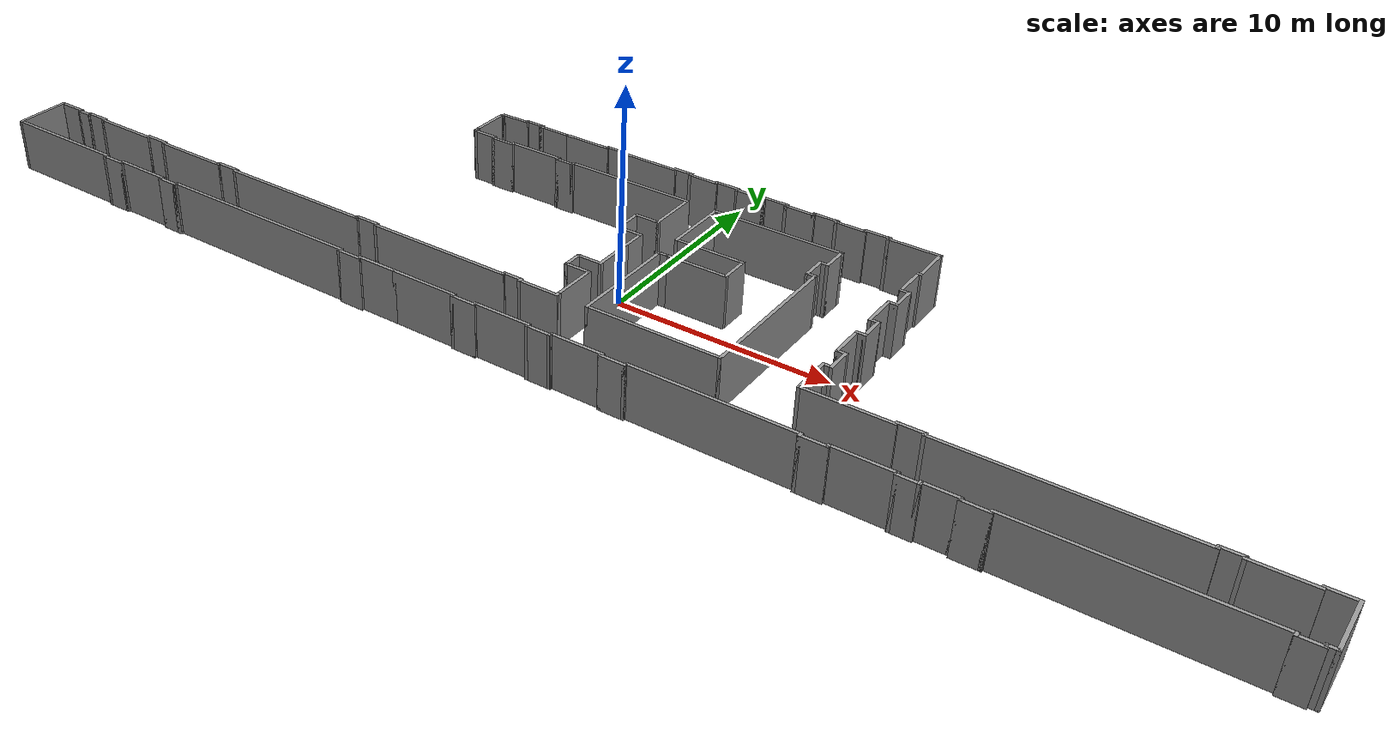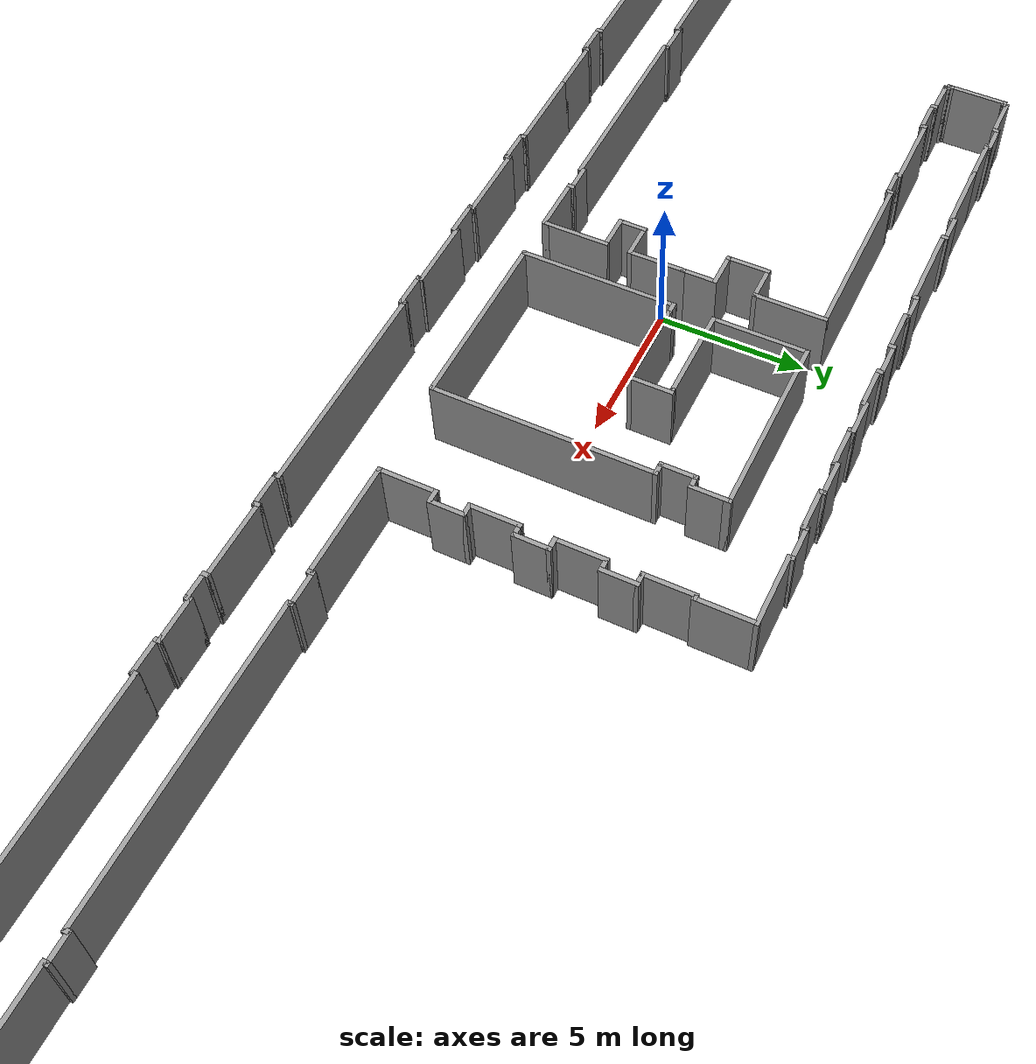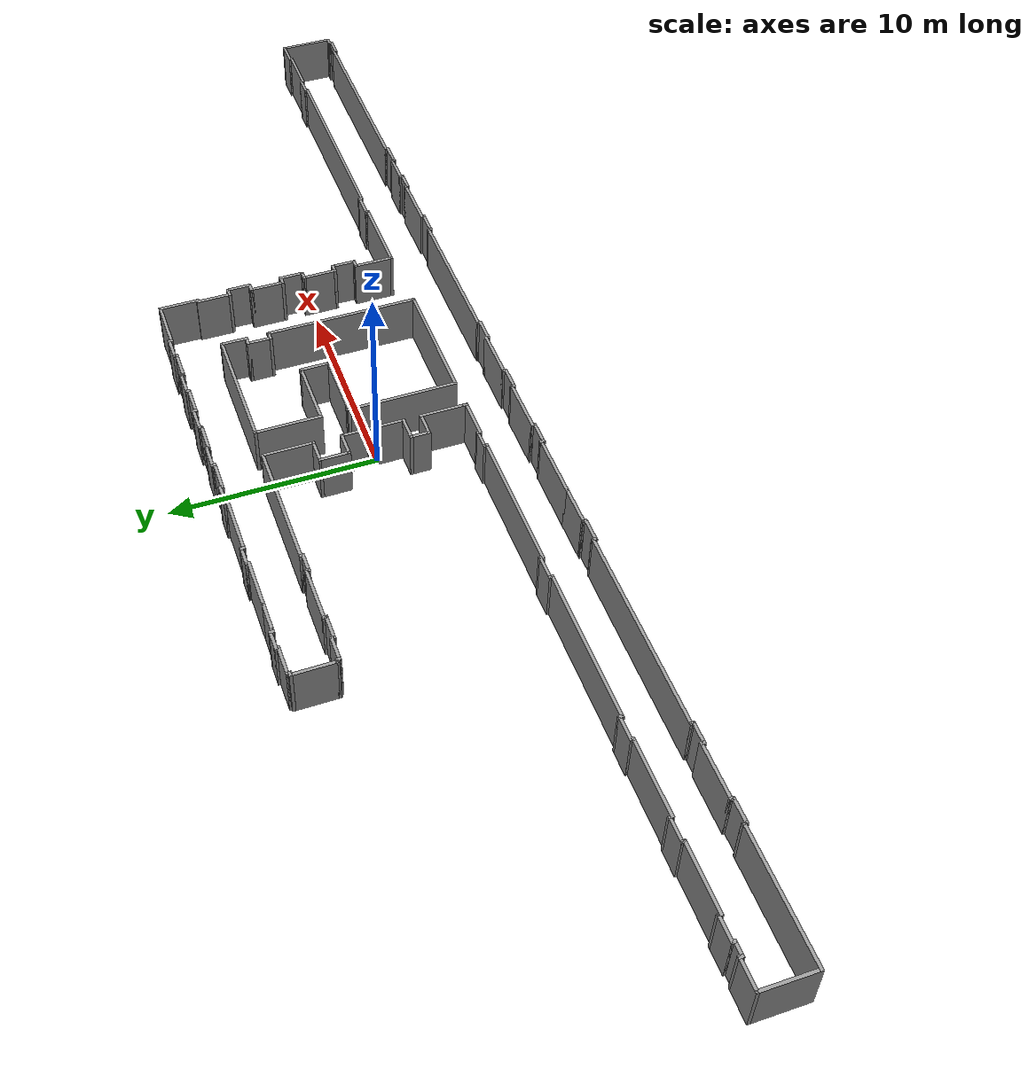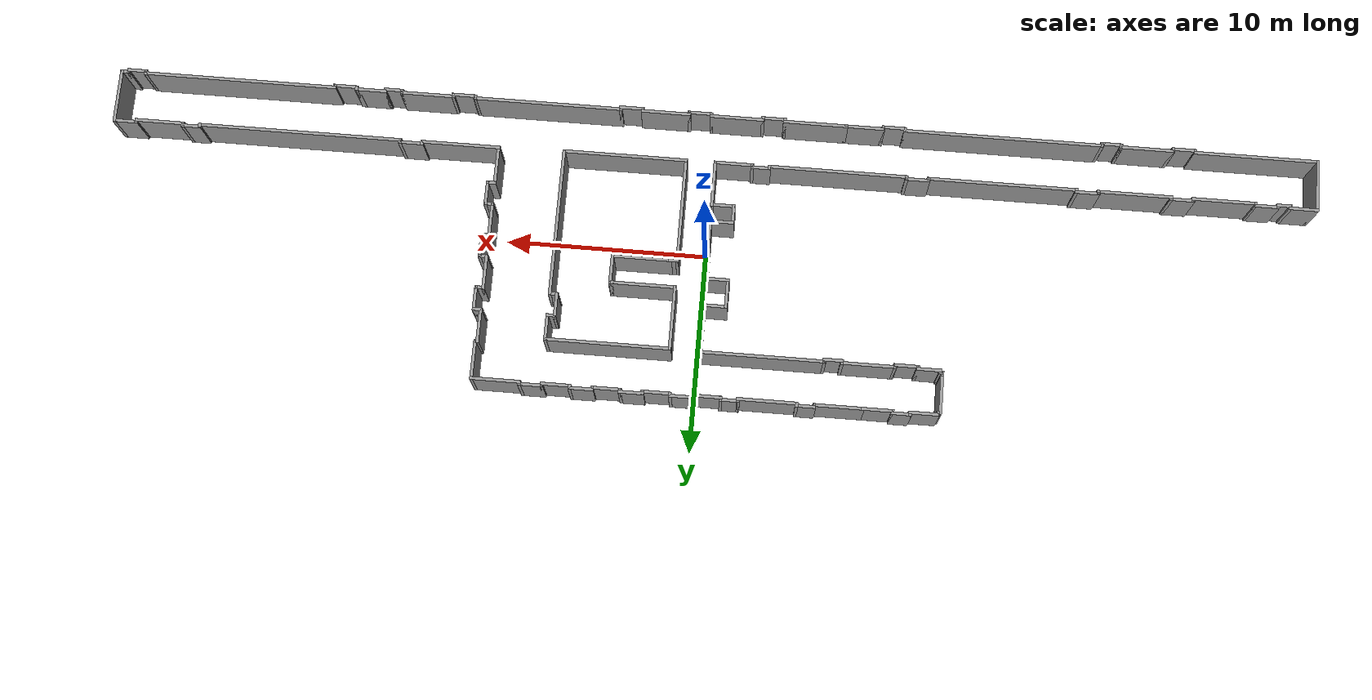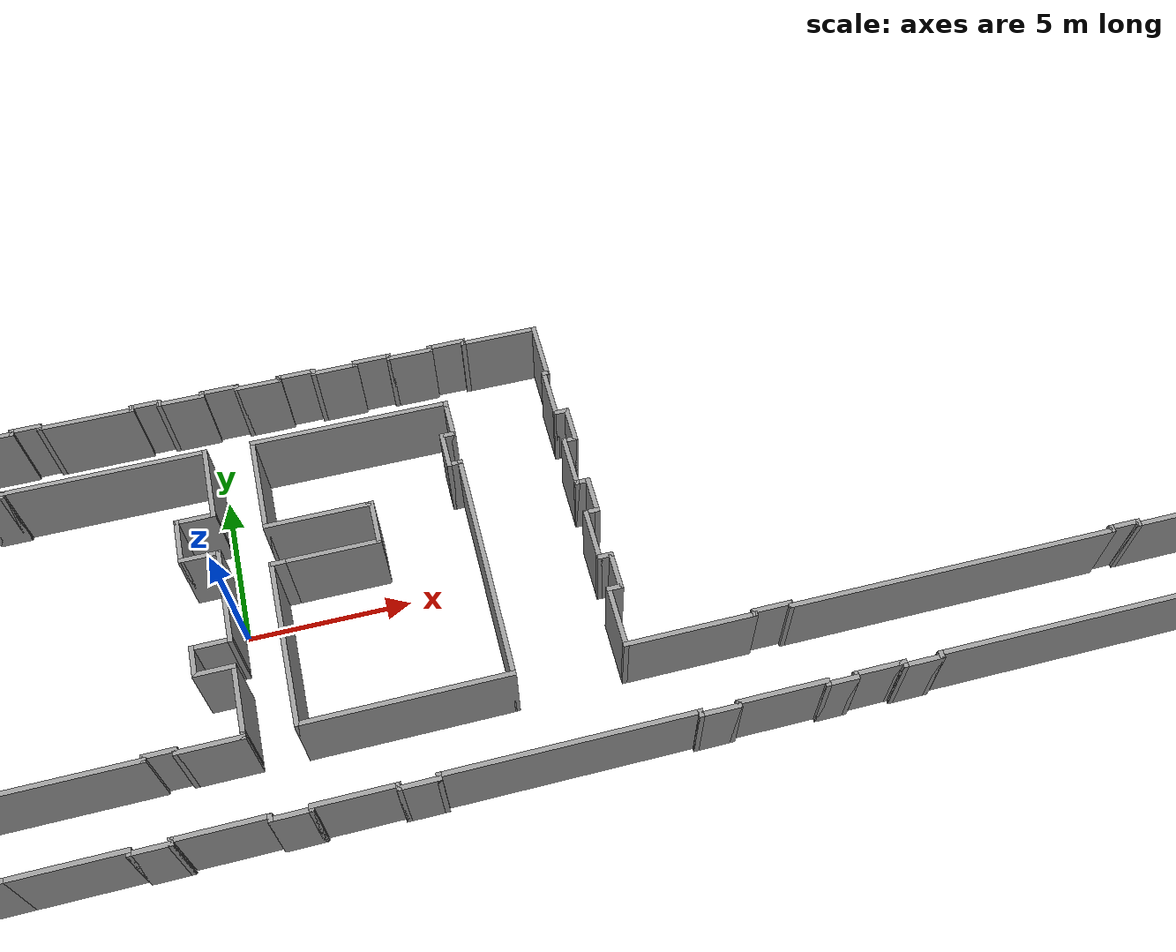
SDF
<?xml version='1.0'?>
<sdf version='1.6'>
  <model name='hallway'>
    <pose frame=''>-0.039388 0.458321 0 0 -0 0</pose>
    <link name='Wall_10'>
      <collision name='Wall_10_Collision'>
        <geometry>
          <box>
            <size>0.25 0.15 2.5</size>
          </box>
        </geometry>
        <pose frame=''>0 0 1.25 0 -0 0</pose>
      </collision>
      <visual name='Wall_10_Visual'>
        <pose frame=''>0 0 1.25 0 -0 0</pose>
        <geometry>
          <box>
            <size>0.25 0.15 2.5</size>
          </box>
        </geometry>
        <material>
          <script>
            <uri>file://media/materials/scripts/gazebo.material</uri>
            <name>Gazebo/Grey</name>
          </script>
          <ambient>1 1 1 1</ambient>
        </material>
      </visual>
      <pose frame=''>-20.275 -7.2 0 0 0 -1.5708</pose>
    </link>
    <link name='Wall_100'>
      <collision name='Wall_100_Collision'>
        <geometry>
          <box>
            <size>3 0.15 2.5</size>
          </box>
        </geometry>
        <pose frame=''>0 0 1.25 0 -0 0</pose>
      </collision>
      <visual name='Wall_100_Visual'>
        <pose frame=''>0 0 1.25 0 -0 0</pose>
        <geometry>
          <box>
            <size>3 0.15 2.5</size>
          </box>
        </geometry>
        <material>
          <script>
            <uri>file://media/materials/scripts/gazebo.material</uri>
            <name>Gazebo/Grey</name>
          </script>
          <ambient>1 1 1 1</ambient>
        </material>
      </visual>
      <pose frame=''>-3.6 7.15 0 0 -0 3.14159</pose>
    </link>
    <link name='Wall_101'>
      <collision name='Wall_101_Collision'>
        <geometry>
          <box>
            <size>0.25 0.15 2.5</size>
          </box>
        </geometry>
        <pose frame=''>0 0 1.25 0 -0 0</pose>
      </collision>
      <visual name='Wall_101_Visual'>
        <pose frame=''>0 0 1.25 0 -0 0</pose>
        <geometry>
          <box>
            <size>0.25 0.15 2.5</size>
          </box>
        </geometry>
        <material>
          <script>
            <uri>file://media/materials/scripts/gazebo.material</uri>
            <name>Gazebo/Grey</name>
          </script>
          <ambient>1 1 1 1</ambient>
        </material>
      </visual>
      <pose frame=''>-5.025 7.2 0 0 -0 1.5708</pose>
    </link>
    <link name='Wall_102'>
      <collision name='Wall_102_Collision'>
        <geometry>
          <box>
            <size>1 0.15 2.5</size>
          </box>
        </geometry>
        <pose frame=''>0 0 1.25 0 -0 0</pose>
      </collision>
      <visual name='Wall_102_Visual'>
        <pose frame=''>0 0 1.25 0 -0 0</pose>
        <geometry>
          <box>
            <size>1 0.15 2.5</size>
          </box>
        </geometry>
        <material>
          <script>
            <uri>file://media/materials/scripts/gazebo.material</uri>
            <name>Gazebo/Grey</name>
          </script>
          <ambient>1 1 1 1</ambient>
        </material>
      </visual>
      <pose frame=''>-5.45 7.25 0 0 -0 3.14159</pose>
    </link>
    <link name='Wall_103'>
      <collision name='Wall_103_Collision'>
        <geometry>
          <box>
            <size>0.25 0.15 2.5</size>
          </box>
        </geometry>
        <pose frame=''>0 0 1.25 0 -0 0</pose>
      </collision>
      <visual name='Wall_103_Visual'>
        <pose frame=''>0 0 1.25 0 -0 0</pose>
        <geometry>
          <box>
            <size>0.25 0.15 2.5</size>
          </box>
        </geometry>
        <material>
          <script>
            <uri>file://media/materials/scripts/gazebo.material</uri>
            <name>Gazebo/Grey</name>
          </script>
          <ambient>1 1 1 1</ambient>
        </material>
      </visual>
      <pose frame=''>-5.875 7.2 0 0 0 -1.5708</pose>
    </link>
    <link name='Wall_104'>
      <collision name='Wall_104_Collision'>
        <geometry>
          <box>
            <size>2.5 0.15 2.5</size>
          </box>
        </geometry>
        <pose frame=''>0 0 1.25 0 -0 0</pose>
      </collision>
      <visual name='Wall_104_Visual'>
        <pose frame=''>0 0 1.25 0 -0 0</pose>
        <geometry>
          <box>
            <size>2.5 0.15 2.5</size>
          </box>
        </geometry>
        <material>
          <script>
            <uri>file://media/materials/scripts/gazebo.material</uri>
            <name>Gazebo/Grey</name>
          </script>
          <ambient>1 1 1 1</ambient>
        </material>
      </visual>
      <pose frame=''>-7.05 7.15 0 0 -0 3.14159</pose>
    </link>
    <link name='Wall_106'>
      <collision name='Wall_106_Collision'>
        <geometry>
          <box>
            <size>1.5 0.15 2.5</size>
          </box>
        </geometry>
        <pose frame=''>0 0 1.25 0 -0 0</pose>
      </collision>
      <visual name='Wall_106_Visual'>
        <pose frame=''>0 0 1.25 0 -0 0</pose>
        <geometry>
          <box>
            <size>1.5 0.15 2.5</size>
          </box>
        </geometry>
        <material>
          <script>
            <uri>file://media/materials/scripts/gazebo.material</uri>
            <name>Gazebo/Grey</name>
          </script>
          <ambient>1 1 1 1</ambient>
        </material>
      </visual>
      <pose frame=''>-8.9 7.15 0 0 -0 3.14159</pose>
    </link>
    <link name='Wall_107'>
      <collision name='Wall_107_Collision'>
        <geometry>
          <box>
            <size>0.25 0.15 2.5</size>
          </box>
        </geometry>
        <pose frame=''>0 0 1.25 0 -0 0</pose>
      </collision>
      <visual name='Wall_107_Visual'>
        <pose frame=''>0 0 1.25 0 -0 0</pose>
        <geometry>
          <box>
            <size>0.25 0.15 2.5</size>
          </box>
        </geometry>
        <material>
          <script>
            <uri>file://media/materials/scripts/gazebo.material</uri>
            <name>Gazebo/Grey</name>
          </script>
          <ambient>1 1 1 1</ambient>
        </material>
      </visual>
      <pose frame=''>-9.625 7.15 0 0 -0 3.14159</pose>
    </link>
    <link name='Wall_108'>
      <collision name='Wall_108_Collision'>
        <geometry>
          <box>
            <size>0.25 0.15 2.5</size>
          </box>
        </geometry>
        <pose frame=''>0 0 1.25 0 -0 0</pose>
      </collision>
      <visual name='Wall_108_Visual'>
        <pose frame=''>0 0 1.25 0 -0 0</pose>
        <geometry>
          <box>
            <size>0.25 0.15 2.5</size>
          </box>
        </geometry>
        <material>
          <script>
            <uri>file://media/materials/scripts/gazebo.material</uri>
            <name>Gazebo/Grey</name>
          </script>
          <ambient>1 1 1 1</ambient>
        </material>
      </visual>
      <pose frame=''>-9.675 7.2 0 0 -0 1.5708</pose>
    </link>
    <link name='Wall_109'>
      <collision name='Wall_109_Collision'>
        <geometry>
          <box>
            <size>1 0.15 2.5</size>
          </box>
        </geometry>
        <pose frame=''>0 0 1.25 0 -0 0</pose>
      </collision>
      <visual name='Wall_109_Visual'>
        <pose frame=''>0 0 1.25 0 -0 0</pose>
        <geometry>
          <box>
            <size>1 0.15 2.5</size>
          </box>
        </geometry>
        <material>
          <script>
            <uri>file://media/materials/scripts/gazebo.material</uri>
            <name>Gazebo/Grey</name>
          </script>
          <ambient>1 1 1 1</ambient>
        </material>
      </visual>
      <pose frame=''>-10.1 7.25 0 0 -0 3.14159</pose>
    </link>
    <link name='Wall_11'>
      <collision name='Wall_11_Collision'>
        <geometry>
          <box>
            <size>1 0.15 2.5</size>
          </box>
        </geometry>
        <pose frame=''>0 0 1.25 0 -0 0</pose>
      </collision>
      <visual name='Wall_11_Visual'>
        <pose frame=''>0 0 1.25 0 -0 0</pose>
        <geometry>
          <box>
            <size>1 0.15 2.5</size>
          </box>
        </geometry>
        <material>
          <script>
            <uri>file://media/materials/scripts/gazebo.material</uri>
            <name>Gazebo/Grey</name>
          </script>
          <ambient>1 1 1 1</ambient>
        </material>
      </visual>
      <pose frame=''>-19.85 -7.25 0 0 -0 0</pose>
    </link>
    <link name='Wall_110'>
      <collision name='Wall_110_Collision'>
        <geometry>
          <box>
            <size>0.25 0.15 2.5</size>
          </box>
        </geometry>
        <pose frame=''>0 0 1.25 0 -0 0</pose>
      </collision>
      <visual name='Wall_110_Visual'>
        <pose frame=''>0 0 1.25 0 -0 0</pose>
        <geometry>
          <box>
            <size>0.25 0.15 2.5</size>
          </box>
        </geometry>
        <material>
          <script>
            <uri>file://media/materials/scripts/gazebo.material</uri>
            <name>Gazebo/Grey</name>
          </script>
          <ambient>1 1 1 1</ambient>
        </material>
      </visual>
      <pose frame=''>-10.525 7.2 0 0 0 -1.5708</pose>
    </link>
    <link name='Wall_111'>
      <collision name='Wall_111_Collision'>
        <geometry>
          <box>
            <size>1.5 0.15 2.5</size>
          </box>
        </geometry>
        <pose frame=''>0 0 1.25 0 -0 0</pose>
      </collision>
      <visual name='Wall_111_Visual'>
        <pose frame=''>0 0 1.25 0 -0 0</pose>
        <geometry>
          <box>
            <size>1.5 0.15 2.5</size>
          </box>
        </geometry>
        <material>
          <script>
            <uri>file://media/materials/scripts/gazebo.material</uri>
            <name>Gazebo/Grey</name>
          </script>
          <ambient>1 1 1 1</ambient>
        </material>
      </visual>
      <pose frame=''>-11.2 7.15 0 0 -0 3.14159</pose>
    </link>
    <link name='Wall_112'>
      <collision name='Wall_112_Collision'>
        <geometry>
          <box>
            <size>0.25 0.15 2.5</size>
          </box>
        </geometry>
        <pose frame=''>0 0 1.25 0 -0 0</pose>
      </collision>
      <visual name='Wall_112_Visual'>
        <pose frame=''>0 0 1.25 0 -0 0</pose>
        <geometry>
          <box>
            <size>0.25 0.15 2.5</size>
          </box>
        </geometry>
        <material>
          <script>
            <uri>file://media/materials/scripts/gazebo.material</uri>
            <name>Gazebo/Grey</name>
          </script>
          <ambient>1 1 1 1</ambient>
        </material>
      </visual>
      <pose frame=''>-11.875 7.1 0 0 0 -1.5708</pose>
    </link>
    <link name='Wall_113'>
      <collision name='Wall_113_Collision'>
        <geometry>
          <box>
            <size>0.25 0.15 2.5</size>
          </box>
        </geometry>
        <pose frame=''>0 0 1.25 0 -0 0</pose>
      </collision>
      <visual name='Wall_113_Visual'>
        <pose frame=''>0 0 1.25 0 -0 0</pose>
        <geometry>
          <box>
            <size>0.25 0.15 2.5</size>
          </box>
        </geometry>
        <material>
          <script>
            <uri>file://media/materials/scripts/gazebo.material</uri>
            <name>Gazebo/Grey</name>
          </script>
          <ambient>1 1 1 1</ambient>
        </material>
      </visual>
      <pose frame=''>-11.925 7.05 0 0 -0 3.14159</pose>
    </link>
    <link name='Wall_114'>
      <collision name='Wall_114_Collision'>
        <geometry>
          <box>
            <size>2.03478 0.15 2.5</size>
          </box>
        </geometry>
        <pose frame=''>0 0 1.25 0 -0 0</pose>
      </collision>
      <visual name='Wall_114_Visual'>
        <pose frame=''>0 0 1.25 0 -0 0</pose>
        <geometry>
          <box>
            <size>2.03478 0.15 2.5</size>
          </box>
        </geometry>
        <material>
          <script>
            <uri>file://media/materials/scripts/gazebo.material</uri>
            <name>Gazebo/Grey</name>
          </script>
          <ambient>1 1 1 1</ambient>
        </material>
      </visual>
      <pose frame=''>-11.975 6.10761 0 0 0 -1.5708</pose>
    </link>
    <link name='Wall_115'>
      <collision name='Wall_115_Collision'>
        <geometry>
          <box>
            <size>0.15 0.15 2.5</size>
          </box>
        </geometry>
        <pose frame=''>0 0 1.25 0 -0 0</pose>
      </collision>
      <visual name='Wall_115_Visual'>
        <pose frame=''>0 0 1.25 0 -0 0</pose>
        <geometry>
          <box>
            <size>0.15 0.15 2.5</size>
          </box>
        </geometry>
        <material>
          <script>
            <uri>file://media/materials/scripts/gazebo.material</uri>
            <name>Gazebo/Grey</name>
          </script>
          <ambient>1 1 1 1</ambient>
        </material>
      </visual>
      <pose frame=''>-11.975 5.16522 0 0 -0 0</pose>
    </link>
    <link name='Wall_12'>
      <collision name='Wall_12_Collision'>
        <geometry>
          <box>
            <size>0.25 0.15 2.5</size>
          </box>
        </geometry>
        <pose frame=''>0 0 1.25 0 -0 0</pose>
      </collision>
      <visual name='Wall_12_Visual'>
        <pose frame=''>0 0 1.25 0 -0 0</pose>
        <geometry>
          <box>
            <size>0.25 0.15 2.5</size>
          </box>
        </geometry>
        <material>
          <script>
            <uri>file://media/materials/scripts/gazebo.material</uri>
            <name>Gazebo/Grey</name>
          </script>
          <ambient>1 1 1 1</ambient>
        </material>
      </visual>
      <pose frame=''>-19.375 -7.25 0 0 -0 0</pose>
    </link>
    <link name='Wall_128'>
      <collision name='Wall_128_Collision'>
        <geometry>
          <box>
            <size>0.25 0.15 2.5</size>
          </box>
        </geometry>
        <pose frame=''>0 0 1.25 0 -0 0</pose>
      </collision>
      <visual name='Wall_128_Visual'>
        <pose frame=''>0 0 1.25 0 -0 0</pose>
        <geometry>
          <box>
            <size>0.25 0.15 2.5</size>
          </box>
        </geometry>
        <material>
          <script>
            <uri>file://media/materials/scripts/gazebo.material</uri>
            <name>Gazebo/Grey</name>
          </script>
          <ambient>1 1 1 1</ambient>
        </material>
      </visual>
      <pose frame=''>-11.975 5.11522 0 0 0 -1.5708</pose>
    </link>
    <link name='Wall_129'>
      <collision name='Wall_129_Collision'>
        <geometry>
          <box>
            <size>0.25 0.15 2.5</size>
          </box>
        </geometry>
        <pose frame=''>0 0 1.25 0 -0 0</pose>
      </collision>
      <visual name='Wall_129_Visual'>
        <pose frame=''>0 0 1.25 0 -0 0</pose>
        <geometry>
          <box>
            <size>0.25 0.15 2.5</size>
          </box>
        </geometry>
        <material>
          <script>
            <uri>file://media/materials/scripts/gazebo.material</uri>
            <name>Gazebo/Grey</name>
          </script>
          <ambient>1 1 1 1</ambient>
        </material>
      </visual>
      <pose frame=''>-11.925 5.06522 0 0 -0 0</pose>
    </link>
    <link name='Wall_13'>
      <collision name='Wall_13_Collision'>
        <geometry>
          <box>
            <size>0.25 0.15 2.5</size>
          </box>
        </geometry>
        <pose frame=''>0 0 1.25 0 -0 0</pose>
      </collision>
      <visual name='Wall_13_Visual'>
        <pose frame=''>0 0 1.25 0 -0 0</pose>
        <geometry>
          <box>
            <size>0.25 0.15 2.5</size>
          </box>
        </geometry>
        <material>
          <script>
            <uri>file://media/materials/scripts/gazebo.material</uri>
            <name>Gazebo/Grey</name>
          </script>
          <ambient>1 1 1 1</ambient>
        </material>
      </visual>
      <pose frame=''>-19.325 -7.2 0 0 -0 1.5708</pose>
    </link>
    <link name='Wall_130'>
      <collision name='Wall_130_Collision'>
        <geometry>
          <box>
            <size>0.25 0.15 2.5</size>
          </box>
        </geometry>
        <pose frame=''>0 0 1.25 0 -0 0</pose>
      </collision>
      <visual name='Wall_130_Visual'>
        <pose frame=''>0 0 1.25 0 -0 0</pose>
        <geometry>
          <box>
            <size>0.25 0.15 2.5</size>
          </box>
        </geometry>
        <material>
          <script>
            <uri>file://media/materials/scripts/gazebo.material</uri>
            <name>Gazebo/Grey</name>
          </script>
          <ambient>1 1 1 1</ambient>
        </material>
      </visual>
      <pose frame=''>-11.875 5.01522 0 0 0 -1.5708</pose>
    </link>
    <link name='Wall_131'>
      <collision name='Wall_131_Collision'>
        <geometry>
          <box>
            <size>1.25 0.15 2.5</size>
          </box>
        </geometry>
        <pose frame=''>0 0 1.25 0 -0 0</pose>
      </collision>
      <visual name='Wall_131_Visual'>
        <pose frame=''>0 0 1.25 0 -0 0</pose>
        <geometry>
          <box>
            <size>1.25 0.15 2.5</size>
          </box>
        </geometry>
        <material>
          <script>
            <uri>file://media/materials/scripts/gazebo.material</uri>
            <name>Gazebo/Grey</name>
          </script>
          <ambient>1 1 1 1</ambient>
        </material>
      </visual>
      <pose frame=''>-11.325 4.96522 0 0 -0 0</pose>
    </link>
    <link name='Wall_132'>
      <collision name='Wall_132_Collision'>
        <geometry>
          <box>
            <size>0.25 0.15 2.5</size>
          </box>
        </geometry>
        <pose frame=''>0 0 1.25 0 -0 0</pose>
      </collision>
      <visual name='Wall_132_Visual'>
        <pose frame=''>0 0 1.25 0 -0 0</pose>
        <geometry>
          <box>
            <size>0.25 0.15 2.5</size>
          </box>
        </geometry>
        <material>
          <script>
            <uri>file://media/materials/scripts/gazebo.material</uri>
            <name>Gazebo/Grey</name>
          </script>
          <ambient>1 1 1 1</ambient>
        </material>
      </visual>
      <pose frame=''>-10.775 4.91522 0 0 0 -1.5708</pose>
    </link>
    <link name='Wall_133'>
      <collision name='Wall_133_Collision'>
        <geometry>
          <box>
            <size>1.25 0.15 2.5</size>
          </box>
        </geometry>
        <pose frame=''>0 0 1.25 0 -0 0</pose>
      </collision>
      <visual name='Wall_133_Visual'>
        <pose frame=''>0 0 1.25 0 -0 0</pose>
        <geometry>
          <box>
            <size>1.25 0.15 2.5</size>
          </box>
        </geometry>
        <material>
          <script>
            <uri>file://media/materials/scripts/gazebo.material</uri>
            <name>Gazebo/Grey</name>
          </script>
          <ambient>1 1 1 1</ambient>
        </material>
      </visual>
      <pose frame=''>-10.225 4.86522 0 0 -0 0</pose>
    </link>
    <link name='Wall_134'>
      <collision name='Wall_134_Collision'>
        <geometry>
          <box>
            <size>0.25 0.15 2.5</size>
          </box>
        </geometry>
        <pose frame=''>0 0 1.25 0 -0 0</pose>
      </collision>
      <visual name='Wall_134_Visual'>
        <pose frame=''>0 0 1.25 0 -0 0</pose>
        <geometry>
          <box>
            <size>0.25 0.15 2.5</size>
          </box>
        </geometry>
        <material>
          <script>
            <uri>file://media/materials/scripts/gazebo.material</uri>
            <name>Gazebo/Grey</name>
          </script>
          <ambient>1 1 1 1</ambient>
        </material>
      </visual>
      <pose frame=''>-9.675 4.91522 0 0 -0 1.5708</pose>
    </link>
    <link name='Wall_135'>
      <collision name='Wall_135_Collision'>
        <geometry>
          <box>
            <size>2.75 0.15 2.5</size>
          </box>
        </geometry>
        <pose frame=''>0 0 1.25 0 -0 0</pose>
      </collision>
      <visual name='Wall_135_Visual'>
        <pose frame=''>0 0 1.25 0 -0 0</pose>
        <geometry>
          <box>
            <size>2.75 0.15 2.5</size>
          </box>
        </geometry>
        <material>
          <script>
            <uri>file://media/materials/scripts/gazebo.material</uri>
            <name>Gazebo/Grey</name>
          </script>
          <ambient>1 1 1 1</ambient>
        </material>
      </visual>
      <pose frame=''>-8.375 4.96522 0 0 -0 0</pose>
    </link>
    <link name='Wall_136'>
      <collision name='Wall_136_Collision'>
        <geometry>
          <box>
            <size>0.25 0.15 2.5</size>
          </box>
        </geometry>
        <pose frame=''>0 0 1.25 0 -0 0</pose>
      </collision>
      <visual name='Wall_136_Visual'>
        <pose frame=''>0 0 1.25 0 -0 0</pose>
        <geometry>
          <box>
            <size>0.25 0.15 2.5</size>
          </box>
        </geometry>
        <material>
          <script>
            <uri>file://media/materials/scripts/gazebo.material</uri>
            <name>Gazebo/Grey</name>
          </script>
          <ambient>1 1 1 1</ambient>
        </material>
      </visual>
      <pose frame=''>-7.075 4.91522 0 0 0 -1.5708</pose>
    </link>
    <link name='Wall_137'>
      <collision name='Wall_137_Collision'>
        <geometry>
          <box>
            <size>1 0.15 2.5</size>
          </box>
        </geometry>
        <pose frame=''>0 0 1.25 0 -0 0</pose>
      </collision>
      <visual name='Wall_137_Visual'>
        <pose frame=''>0 0 1.25 0 -0 0</pose>
        <geometry>
          <box>
            <size>1 0.15 2.5</size>
          </box>
        </geometry>
        <material>
          <script>
            <uri>file://media/materials/scripts/gazebo.material</uri>
            <name>Gazebo/Grey</name>
          </script>
          <ambient>1 1 1 1</ambient>
        </material>
      </visual>
      <pose frame=''>-6.65 4.86522 0 0 -0 0</pose>
    </link>
    <link name='Wall_138'>
      <collision name='Wall_138_Collision'>
        <geometry>
          <box>
            <size>0.25 0.15 2.5</size>
          </box>
        </geometry>
        <pose frame=''>0 0 1.25 0 -0 0</pose>
      </collision>
      <visual name='Wall_138_Visual'>
        <pose frame=''>0 0 1.25 0 -0 0</pose>
        <geometry>
          <box>
            <size>0.25 0.15 2.5</size>
          </box>
        </geometry>
        <material>
          <script>
            <uri>file://media/materials/scripts/gazebo.material</uri>
            <name>Gazebo/Grey</name>
          </script>
          <ambient>1 1 1 1</ambient>
        </material>
      </visual>
      <pose frame=''>-6.225 4.91522 0 0 -0 1.5708</pose>
    </link>
    <link name='Wall_139'>
      <collision name='Wall_139_Collision'>
        <geometry>
          <box>
            <size>6.25 0.15 2.5</size>
          </box>
        </geometry>
        <pose frame=''>0 0 1.25 0 -0 0</pose>
      </collision>
      <visual name='Wall_139_Visual'>
        <pose frame=''>0 0 1.25 0 -0 0</pose>
        <geometry>
          <box>
            <size>6.25 0.15 2.5</size>
          </box>
        </geometry>
        <material>
          <script>
            <uri>file://media/materials/scripts/gazebo.material</uri>
            <name>Gazebo/Grey</name>
          </script>
          <ambient>1 1 1 1</ambient>
        </material>
      </visual>
      <pose frame=''>-3.175 4.96522 0 0 -0 0</pose>
    </link>
    <link name='Wall_14'>
      <collision name='Wall_14_Collision'>
        <geometry>
          <box>
            <size>10 0.15 2.5</size>
          </box>
        </geometry>
        <pose frame=''>0 0 1.25 0 -0 0</pose>
      </collision>
      <visual name='Wall_14_Visual'>
        <pose frame=''>0 0 1.25 0 -0 0</pose>
        <geometry>
          <box>
            <size>10 0.15 2.5</size>
          </box>
        </geometry>
        <material>
          <script>
            <uri>file://media/materials/scripts/gazebo.material</uri>
            <name>Gazebo/Grey</name>
          </script>
          <ambient>1 1 1 1</ambient>
        </material>
      </visual>
      <pose frame=''>-14.4 -7.15 0 0 -0 0</pose>
    </link>
    <link name='Wall_140'>
      <collision name='Wall_140_Collision'>
        <geometry>
          <box>
            <size>2.5 0.15 2.5</size>
          </box>
        </geometry>
        <pose frame=''>0 0 1.25 0 -0 0</pose>
      </collision>
      <visual name='Wall_140_Visual'>
        <pose frame=''>0 0 1.25 0 -0 0</pose>
        <geometry>
          <box>
            <size>2.5 0.15 2.5</size>
          </box>
        </geometry>
        <material>
          <script>
            <uri>file://media/materials/scripts/gazebo.material</uri>
            <name>Gazebo/Grey</name>
          </script>
          <ambient>1 1 1 1</ambient>
        </material>
      </visual>
      <pose frame=''>-0.125 3.79022 0 0 0 -1.5708</pose>
    </link>
    <link name='Wall_141'>
      <collision name='Wall_141_Collision'>
        <geometry>
          <box>
            <size>1.25 0.15 2.5</size>
          </box>
        </geometry>
        <pose frame=''>0 0 1.25 0 -0 0</pose>
      </collision>
      <visual name='Wall_141_Visual'>
        <pose frame=''>0 0 1.25 0 -0 0</pose>
        <geometry>
          <box>
            <size>1.25 0.15 2.5</size>
          </box>
        </geometry>
        <material>
          <script>
            <uri>file://media/materials/scripts/gazebo.material</uri>
            <name>Gazebo/Grey</name>
          </script>
          <ambient>1 1 1 1</ambient>
        </material>
      </visual>
      <pose frame=''>-0.675 2.61522 0 0 -0 3.14159</pose>
    </link>
    <link name='Wall_142'>
      <collision name='Wall_142_Collision'>
        <geometry>
          <box>
            <size>1.5 0.15 2.5</size>
          </box>
        </geometry>
        <pose frame=''>0 0 1.25 0 -0 0</pose>
      </collision>
      <visual name='Wall_142_Visual'>
        <pose frame=''>0 0 1.25 0 -0 0</pose>
        <geometry>
          <box>
            <size>1.5 0.15 2.5</size>
          </box>
        </geometry>
        <material>
          <script>
            <uri>file://media/materials/scripts/gazebo.material</uri>
            <name>Gazebo/Grey</name>
          </script>
          <ambient>1 1 1 1</ambient>
        </material>
      </visual>
      <pose frame=''>-1.225 1.94022 0 0 0 -1.5708</pose>
    </link>
    <link name='Wall_143'>
      <collision name='Wall_143_Collision'>
        <geometry>
          <box>
            <size>1.25 0.15 2.5</size>
          </box>
        </geometry>
        <pose frame=''>0 0 1.25 0 -0 0</pose>
      </collision>
      <visual name='Wall_143_Visual'>
        <pose frame=''>0 0 1.25 0 -0 0</pose>
        <geometry>
          <box>
            <size>1.25 0.15 2.5</size>
          </box>
        </geometry>
        <material>
          <script>
            <uri>file://media/materials/scripts/gazebo.material</uri>
            <name>Gazebo/Grey</name>
          </script>
          <ambient>1 1 1 1</ambient>
        </material>
      </visual>
      <pose frame=''>-0.675 1.26522 0 0 -0 0</pose>
    </link>
    <link name='Wall_144'>
      <collision name='Wall_144_Collision'>
        <geometry>
          <box>
            <size>1.25 0.15 2.5</size>
          </box>
        </geometry>
        <pose frame=''>0 0 1.25 0 -0 0</pose>
      </collision>
      <visual name='Wall_144_Visual'>
        <pose frame=''>0 0 1.25 0 -0 0</pose>
        <geometry>
          <box>
            <size>1.25 0.15 2.5</size>
          </box>
        </geometry>
        <material>
          <script>
            <uri>file://media/materials/scripts/gazebo.material</uri>
            <name>Gazebo/Grey</name>
          </script>
          <ambient>1 1 1 1</ambient>
        </material>
      </visual>
      <pose frame=''>-0.125 0.715217 0 0 0 -1.5708</pose>
    </link>
    <link name='Wall_146'>
      <collision name='Wall_146_Collision'>
        <geometry>
          <box>
            <size>2 0.15 2.5</size>
          </box>
        </geometry>
        <pose frame=''>0 0 1.25 0 -0 0</pose>
      </collision>
      <visual name='Wall_146_Visual'>
        <pose frame=''>0 0 1.25 0 -0 0</pose>
        <geometry>
          <box>
            <size>2 0.15 2.5</size>
          </box>
        </geometry>
        <material>
          <script>
            <uri>file://media/materials/scripts/gazebo.material</uri>
            <name>Gazebo/Grey</name>
          </script>
          <ambient>1 1 1 1</ambient>
        </material>
      </visual>
      <pose frame=''>-0.125 -0.759783 0 0 0 -1.5708</pose>
    </link>
    <link name='Wall_147'>
      <collision name='Wall_147_Collision'>
        <geometry>
          <box>
            <size>1.25 0.15 2.5</size>
          </box>
        </geometry>
        <pose frame=''>0 0 1.25 0 -0 0</pose>
      </collision>
      <visual name='Wall_147_Visual'>
        <pose frame=''>0 0 1.25 0 -0 0</pose>
        <geometry>
          <box>
            <size>1.25 0.15 2.5</size>
          </box>
        </geometry>
        <material>
          <script>
            <uri>file://media/materials/scripts/gazebo.material</uri>
            <name>Gazebo/Grey</name>
          </script>
          <ambient>1 1 1 1</ambient>
        </material>
      </visual>
      <pose frame=''>-0.675 -1.68478 0 0 -0 3.14159</pose>
    </link>
    <link name='Wall_148'>
      <collision name='Wall_148_Collision'>
        <geometry>
          <box>
            <size>1 0.15 2.5</size>
          </box>
        </geometry>
        <pose frame=''>0 0 1.25 0 -0 0</pose>
      </collision>
      <visual name='Wall_148_Visual'>
        <pose frame=''>0 0 1.25 0 -0 0</pose>
        <geometry>
          <box>
            <size>1 0.15 2.5</size>
          </box>
        </geometry>
        <material>
          <script>
            <uri>file://media/materials/scripts/gazebo.material</uri>
            <name>Gazebo/Grey</name>
          </script>
          <ambient>1 1 1 1</ambient>
        </material>
      </visual>
      <pose frame=''>-1.225 -2.10978 0 0 0 -1.5708</pose>
    </link>
    <link name='Wall_15'>
      <collision name='Wall_15_Collision'>
        <geometry>
          <box>
            <size>0.25 0.15 2.5</size>
          </box>
        </geometry>
        <pose frame=''>0 0 1.25 0 -0 0</pose>
      </collision>
      <visual name='Wall_15_Visual'>
        <pose frame=''>0 0 1.25 0 -0 0</pose>
        <geometry>
          <box>
            <size>0.25 0.15 2.5</size>
          </box>
        </geometry>
        <material>
          <script>
            <uri>file://media/materials/scripts/gazebo.material</uri>
            <name>Gazebo/Grey</name>
          </script>
          <ambient>1 1 1 1</ambient>
        </material>
      </visual>
      <pose frame=''>-9.475 -7.2 0 0 0 -1.5708</pose>
    </link>
    <link name='Wall_156'>
      <collision name='Wall_156_Collision'>
        <geometry>
          <box>
            <size>1.25 0.15 2.5</size>
          </box>
        </geometry>
        <pose frame=''>0 0 1.25 0 -0 0</pose>
      </collision>
      <visual name='Wall_156_Visual'>
        <pose frame=''>0 0 1.25 0 -0 0</pose>
        <geometry>
          <box>
            <size>1.25 0.15 2.5</size>
          </box>
        </geometry>
        <material>
          <script>
            <uri>file://media/materials/scripts/gazebo.material</uri>
            <name>Gazebo/Grey</name>
          </script>
          <ambient>1 1 1 1</ambient>
        </material>
      </visual>
      <pose frame=''>-0.675 -2.53478 0 0 -0 0</pose>
    </link>
    <link name='Wall_157'>
      <collision name='Wall_157_Collision'>
        <geometry>
          <box>
            <size>2.25 0.15 2.5</size>
          </box>
        </geometry>
        <pose frame=''>0 0 1.25 0 -0 0</pose>
      </collision>
      <visual name='Wall_157_Visual'>
        <pose frame=''>0 0 1.25 0 -0 0</pose>
        <geometry>
          <box>
            <size>2.25 0.15 2.5</size>
          </box>
        </geometry>
        <material>
          <script>
            <uri>file://media/materials/scripts/gazebo.material</uri>
            <name>Gazebo/Grey</name>
          </script>
          <ambient>1 1 1 1</ambient>
        </material>
      </visual>
      <pose frame=''>-0.125 -3.58478 0 0 0 -1.5708</pose>
    </link>
    <link name='Wall_158'>
      <collision name='Wall_158_Collision'>
        <geometry>
          <box>
            <size>0.25 0.15 2.5</size>
          </box>
        </geometry>
        <pose frame=''>0 0 1.25 0 -0 0</pose>
      </collision>
      <visual name='Wall_158_Visual'>
        <pose frame=''>0 0 1.25 0 -0 0</pose>
        <geometry>
          <box>
            <size>0.25 0.15 2.5</size>
          </box>
        </geometry>
        <material>
          <script>
            <uri>file://media/materials/scripts/gazebo.material</uri>
            <name>Gazebo/Grey</name>
          </script>
          <ambient>1 1 1 1</ambient>
        </material>
      </visual>
      <pose frame=''>-0.125 -4.68478 0 0 0 -1.5708</pose>
    </link>
    <link name='Wall_159'>
      <collision name='Wall_159_Collision'>
        <geometry>
          <box>
            <size>2 0.15 2.5</size>
          </box>
        </geometry>
        <pose frame=''>0 0 1.25 0 -0 0</pose>
      </collision>
      <visual name='Wall_159_Visual'>
        <pose frame=''>0 0 1.25 0 -0 0</pose>
        <geometry>
          <box>
            <size>2 0.15 2.5</size>
          </box>
        </geometry>
        <material>
          <script>
            <uri>file://media/materials/scripts/gazebo.material</uri>
            <name>Gazebo/Grey</name>
          </script>
          <ambient>1 1 1 1</ambient>
        </material>
      </visual>
      <pose frame=''>-1.05 -4.73478 0 0 -0 3.14159</pose>
    </link>
    <link name='Wall_16'>
      <collision name='Wall_16_Collision'>
        <geometry>
          <box>
            <size>1.25 0.15 2.5</size>
          </box>
        </geometry>
        <pose frame=''>0 0 1.25 0 -0 0</pose>
      </collision>
      <visual name='Wall_16_Visual'>
        <pose frame=''>0 0 1.25 0 -0 0</pose>
        <geometry>
          <box>
            <size>1.25 0.15 2.5</size>
          </box>
        </geometry>
        <material>
          <script>
            <uri>file://media/materials/scripts/gazebo.material</uri>
            <name>Gazebo/Grey</name>
          </script>
          <ambient>1 1 1 1</ambient>
        </material>
      </visual>
      <pose frame=''>-8.925 -7.25 0 0 -0 0</pose>
    </link>
    <link name='Wall_160'>
      <collision name='Wall_160_Collision'>
        <geometry>
          <box>
            <size>0.25 0.15 2.5</size>
          </box>
        </geometry>
        <pose frame=''>0 0 1.25 0 -0 0</pose>
      </collision>
      <visual name='Wall_160_Visual'>
        <pose frame=''>0 0 1.25 0 -0 0</pose>
        <geometry>
          <box>
            <size>0.25 0.15 2.5</size>
          </box>
        </geometry>
        <material>
          <script>
            <uri>file://media/materials/scripts/gazebo.material</uri>
            <name>Gazebo/Grey</name>
          </script>
          <ambient>1 1 1 1</ambient>
        </material>
      </visual>
      <pose frame=''>-1.975 -4.68478 0 0 -0 1.5708</pose>
    </link>
    <link name='Wall_161'>
      <collision name='Wall_161_Collision'>
        <geometry>
          <box>
            <size>1 0.15 2.5</size>
          </box>
        </geometry>
        <pose frame=''>0 0 1.25 0 -0 0</pose>
      </collision>
      <visual name='Wall_161_Visual'>
        <pose frame=''>0 0 1.25 0 -0 0</pose>
        <geometry>
          <box>
            <size>1 0.15 2.5</size>
          </box>
        </geometry>
        <material>
          <script>
            <uri>file://media/materials/scripts/gazebo.material</uri>
            <name>Gazebo/Grey</name>
          </script>
          <ambient>1 1 1 1</ambient>
        </material>
      </visual>
      <pose frame=''>-2.4 -4.63478 0 0 -0 3.14159</pose>
    </link>
    <link name='Wall_162'>
      <collision name='Wall_162_Collision'>
        <geometry>
          <box>
            <size>0.25 0.15 2.5</size>
          </box>
        </geometry>
        <pose frame=''>0 0 1.25 0 -0 0</pose>
      </collision>
      <visual name='Wall_162_Visual'>
        <pose frame=''>0 0 1.25 0 -0 0</pose>
        <geometry>
          <box>
            <size>0.25 0.15 2.5</size>
          </box>
        </geometry>
        <material>
          <script>
            <uri>file://media/materials/scripts/gazebo.material</uri>
            <name>Gazebo/Grey</name>
          </script>
          <ambient>1 1 1 1</ambient>
        </material>
      </visual>
      <pose frame=''>-2.825 -4.68478 0 0 0 -1.5708</pose>
    </link>
    <link name='Wall_163'>
      <collision name='Wall_163_Collision'>
        <geometry>
          <box>
            <size>7 0.15 2.5</size>
          </box>
        </geometry>
        <pose frame=''>0 0 1.25 0 -0 0</pose>
      </collision>
      <visual name='Wall_163_Visual'>
        <pose frame=''>0 0 1.25 0 -0 0</pose>
        <geometry>
          <box>
            <size>7 0.15 2.5</size>
          </box>
        </geometry>
        <material>
          <script>
            <uri>file://media/materials/scripts/gazebo.material</uri>
            <name>Gazebo/Grey</name>
          </script>
          <ambient>1 1 1 1</ambient>
        </material>
      </visual>
      <pose frame=''>-6.25 -4.73478 0 0 -0 3.14159</pose>
    </link>
    <link name='Wall_164'>
      <collision name='Wall_164_Collision'>
        <geometry>
          <box>
            <size>0.25 0.15 2.5</size>
          </box>
        </geometry>
        <pose frame=''>0 0 1.25 0 -0 0</pose>
      </collision>
      <visual name='Wall_164_Visual'>
        <pose frame=''>0 0 1.25 0 -0 0</pose>
        <geometry>
          <box>
            <size>0.25 0.15 2.5</size>
          </box>
        </geometry>
        <material>
          <script>
            <uri>file://media/materials/scripts/gazebo.material</uri>
            <name>Gazebo/Grey</name>
          </script>
          <ambient>1 1 1 1</ambient>
        </material>
      </visual>
      <pose frame=''>-9.675 -4.68478 0 0 -0 1.5708</pose>
    </link>
    <link name='Wall_165'>
      <collision name='Wall_165_Collision'>
        <geometry>
          <box>
            <size>1.25 0.15 2.5</size>
          </box>
        </geometry>
        <pose frame=''>0 0 1.25 0 -0 0</pose>
      </collision>
      <visual name='Wall_165_Visual'>
        <pose frame=''>0 0 1.25 0 -0 0</pose>
        <geometry>
          <box>
            <size>1.25 0.15 2.5</size>
          </box>
        </geometry>
        <material>
          <script>
            <uri>file://media/materials/scripts/gazebo.material</uri>
            <name>Gazebo/Grey</name>
          </script>
          <ambient>1 1 1 1</ambient>
        </material>
      </visual>
      <pose frame=''>-10.225 -4.63478 0 0 -0 3.14159</pose>
    </link>
    <link name='Wall_166'>
      <collision name='Wall_166_Collision'>
        <geometry>
          <box>
            <size>0.25 0.15 2.5</size>
          </box>
        </geometry>
        <pose frame=''>0 0 1.25 0 -0 0</pose>
      </collision>
      <visual name='Wall_166_Visual'>
        <pose frame=''>0 0 1.25 0 -0 0</pose>
        <geometry>
          <box>
            <size>0.25 0.15 2.5</size>
          </box>
        </geometry>
        <material>
          <script>
            <uri>file://media/materials/scripts/gazebo.material</uri>
            <name>Gazebo/Grey</name>
          </script>
          <ambient>1 1 1 1</ambient>
        </material>
      </visual>
      <pose frame=''>-10.775 -4.68478 0 0 0 -1.5708</pose>
    </link>
    <link name='Wall_167'>
      <collision name='Wall_167_Collision'>
        <geometry>
          <box>
            <size>7.5 0.15 2.5</size>
          </box>
        </geometry>
        <pose frame=''>0 0 1.25 0 -0 0</pose>
      </collision>
      <visual name='Wall_167_Visual'>
        <pose frame=''>0 0 1.25 0 -0 0</pose>
        <geometry>
          <box>
            <size>7.5 0.15 2.5</size>
          </box>
        </geometry>
        <material>
          <script>
            <uri>file://media/materials/scripts/gazebo.material</uri>
            <name>Gazebo/Grey</name>
          </script>
          <ambient>1 1 1 1</ambient>
        </material>
      </visual>
      <pose frame=''>-14.45 -4.73478 0 0 -0 3.14159</pose>
    </link>
    <link name='Wall_168'>
      <collision name='Wall_168_Collision'>
        <geometry>
          <box>
            <size>0.25 0.15 2.5</size>
          </box>
        </geometry>
        <pose frame=''>0 0 1.25 0 -0 0</pose>
      </collision>
      <visual name='Wall_168_Visual'>
        <pose frame=''>0 0 1.25 0 -0 0</pose>
        <geometry>
          <box>
            <size>0.25 0.15 2.5</size>
          </box>
        </geometry>
        <material>
          <script>
            <uri>file://media/materials/scripts/gazebo.material</uri>
            <name>Gazebo/Grey</name>
          </script>
          <ambient>1 1 1 1</ambient>
        </material>
      </visual>
      <pose frame=''>-18.125 -4.68478 0 0 -0 1.5708</pose>
    </link>
    <link name='Wall_169'>
      <collision name='Wall_169_Collision'>
        <geometry>
          <box>
            <size>1.25 0.15 2.5</size>
          </box>
        </geometry>
        <pose frame=''>0 0 1.25 0 -0 0</pose>
      </collision>
      <visual name='Wall_169_Visual'>
        <pose frame=''>0 0 1.25 0 -0 0</pose>
        <geometry>
          <box>
            <size>1.25 0.15 2.5</size>
          </box>
        </geometry>
        <material>
          <script>
            <uri>file://media/materials/scripts/gazebo.material</uri>
            <name>Gazebo/Grey</name>
          </script>
          <ambient>1 1 1 1</ambient>
        </material>
      </visual>
      <pose frame=''>-18.675 -4.63478 0 0 -0 3.14159</pose>
    </link>
    <link name='Wall_17'>
      <collision name='Wall_17_Collision'>
        <geometry>
          <box>
            <size>0.25 0.15 2.5</size>
          </box>
        </geometry>
        <pose frame=''>0 0 1.25 0 -0 0</pose>
      </collision>
      <visual name='Wall_17_Visual'>
        <pose frame=''>0 0 1.25 0 -0 0</pose>
        <geometry>
          <box>
            <size>0.25 0.15 2.5</size>
          </box>
        </geometry>
        <material>
          <script>
            <uri>file://media/materials/scripts/gazebo.material</uri>
            <name>Gazebo/Grey</name>
          </script>
          <ambient>1 1 1 1</ambient>
        </material>
      </visual>
      <pose frame=''>-8.375 -7.2 0 0 -0 1.5708</pose>
    </link>
    <link name='Wall_170'>
      <collision name='Wall_170_Collision'>
        <geometry>
          <box>
            <size>0.25 0.15 2.5</size>
          </box>
        </geometry>
        <pose frame=''>0 0 1.25 0 -0 0</pose>
      </collision>
      <visual name='Wall_170_Visual'>
        <pose frame=''>0 0 1.25 0 -0 0</pose>
        <geometry>
          <box>
            <size>0.25 0.15 2.5</size>
          </box>
        </geometry>
        <material>
          <script>
            <uri>file://media/materials/scripts/gazebo.material</uri>
            <name>Gazebo/Grey</name>
          </script>
          <ambient>1 1 1 1</ambient>
        </material>
      </visual>
      <pose frame=''>-19.225 -4.68478 0 0 0 -1.5708</pose>
    </link>
    <link name='Wall_171'>
      <collision name='Wall_171_Collision'>
        <geometry>
          <box>
            <size>3.75 0.15 2.5</size>
          </box>
        </geometry>
        <pose frame=''>0 0 1.25 0 -0 0</pose>
      </collision>
      <visual name='Wall_171_Visual'>
        <pose frame=''>0 0 1.25 0 -0 0</pose>
        <geometry>
          <box>
            <size>3.75 0.15 2.5</size>
          </box>
        </geometry>
        <material>
          <script>
            <uri>file://media/materials/scripts/gazebo.material</uri>
            <name>Gazebo/Grey</name>
          </script>
          <ambient>1 1 1 1</ambient>
        </material>
      </visual>
      <pose frame=''>-21.025 -4.73478 0 0 -0 3.14159</pose>
    </link>
    <link name='Wall_172'>
      <collision name='Wall_172_Collision'>
        <geometry>
          <box>
            <size>0.25 0.15 2.5</size>
          </box>
        </geometry>
        <pose frame=''>0 0 1.25 0 -0 0</pose>
      </collision>
      <visual name='Wall_172_Visual'>
        <pose frame=''>0 0 1.25 0 -0 0</pose>
        <geometry>
          <box>
            <size>0.25 0.15 2.5</size>
          </box>
        </geometry>
        <material>
          <script>
            <uri>file://media/materials/scripts/gazebo.material</uri>
            <name>Gazebo/Grey</name>
          </script>
          <ambient>1 1 1 1</ambient>
        </material>
      </visual>
      <pose frame=''>-22.825 -4.68478 0 0 -0 1.5708</pose>
    </link>
    <link name='Wall_173'>
      <collision name='Wall_173_Collision'>
        <geometry>
          <box>
            <size>1.25 0.15 2.5</size>
          </box>
        </geometry>
        <pose frame=''>0 0 1.25 0 -0 0</pose>
      </collision>
      <visual name='Wall_173_Visual'>
        <pose frame=''>0 0 1.25 0 -0 0</pose>
        <geometry>
          <box>
            <size>1.25 0.15 2.5</size>
          </box>
        </geometry>
        <material>
          <script>
            <uri>file://media/materials/scripts/gazebo.material</uri>
            <name>Gazebo/Grey</name>
          </script>
          <ambient>1 1 1 1</ambient>
        </material>
      </visual>
      <pose frame=''>-23.375 -4.63478 0 0 -0 3.14159</pose>
    </link>
    <link name='Wall_174'>
      <collision name='Wall_174_Collision'>
        <geometry>
          <box>
            <size>0.25 0.15 2.5</size>
          </box>
        </geometry>
        <pose frame=''>0 0 1.25 0 -0 0</pose>
      </collision>
      <visual name='Wall_174_Visual'>
        <pose frame=''>0 0 1.25 0 -0 0</pose>
        <geometry>
          <box>
            <size>0.25 0.15 2.5</size>
          </box>
        </geometry>
        <material>
          <script>
            <uri>file://media/materials/scripts/gazebo.material</uri>
            <name>Gazebo/Grey</name>
          </script>
          <ambient>1 1 1 1</ambient>
        </material>
      </visual>
      <pose frame=''>-23.925 -4.68478 0 0 0 -1.5708</pose>
    </link>
    <link name='Wall_175'>
      <collision name='Wall_175_Collision'>
        <geometry>
          <box>
            <size>3.25 0.15 2.5</size>
          </box>
        </geometry>
        <pose frame=''>0 0 1.25 0 -0 0</pose>
      </collision>
      <visual name='Wall_175_Visual'>
        <pose frame=''>0 0 1.25 0 -0 0</pose>
        <geometry>
          <box>
            <size>3.25 0.15 2.5</size>
          </box>
        </geometry>
        <material>
          <script>
            <uri>file://media/materials/scripts/gazebo.material</uri>
            <name>Gazebo/Grey</name>
          </script>
          <ambient>1 1 1 1</ambient>
        </material>
      </visual>
      <pose frame=''>-25.475 -4.73478 0 0 -0 3.14159</pose>
    </link>
    <link name='Wall_176'>
      <collision name='Wall_176_Collision'>
        <geometry>
          <box>
            <size>0.25 0.15 2.5</size>
          </box>
        </geometry>
        <pose frame=''>0 0 1.25 0 -0 0</pose>
      </collision>
      <visual name='Wall_176_Visual'>
        <pose frame=''>0 0 1.25 0 -0 0</pose>
        <geometry>
          <box>
            <size>0.25 0.15 2.5</size>
          </box>
        </geometry>
        <material>
          <script>
            <uri>file://media/materials/scripts/gazebo.material</uri>
            <name>Gazebo/Grey</name>
          </script>
          <ambient>1 1 1 1</ambient>
        </material>
      </visual>
      <pose frame=''>-27.025 -4.68478 0 0 -0 1.5708</pose>
    </link>
    <link name='Wall_177'>
      <collision name='Wall_177_Collision'>
        <geometry>
          <box>
            <size>1.25 0.15 2.5</size>
          </box>
        </geometry>
        <pose frame=''>0 0 1.25 0 -0 0</pose>
      </collision>
      <visual name='Wall_177_Visual'>
        <pose frame=''>0 0 1.25 0 -0 0</pose>
        <geometry>
          <box>
            <size>1.25 0.15 2.5</size>
          </box>
        </geometry>
        <material>
          <script>
            <uri>file://media/materials/scripts/gazebo.material</uri>
            <name>Gazebo/Grey</name>
          </script>
          <ambient>1 1 1 1</ambient>
        </material>
      </visual>
      <pose frame=''>-27.575 -4.63478 0 0 -0 3.14159</pose>
    </link>
    <link name='Wall_178'>
      <collision name='Wall_178_Collision'>
        <geometry>
          <box>
            <size>0.25 0.15 2.5</size>
          </box>
        </geometry>
        <pose frame=''>0 0 1.25 0 -0 0</pose>
      </collision>
      <visual name='Wall_178_Visual'>
        <pose frame=''>0 0 1.25 0 -0 0</pose>
        <geometry>
          <box>
            <size>0.25 0.15 2.5</size>
          </box>
        </geometry>
        <material>
          <script>
            <uri>file://media/materials/scripts/gazebo.material</uri>
            <name>Gazebo/Grey</name>
          </script>
          <ambient>1 1 1 1</ambient>
        </material>
      </visual>
      <pose frame=''>-28.125 -4.68478 0 0 0 -1.5708</pose>
    </link>
    <link name='Wall_179'>
      <collision name='Wall_179_Collision'>
        <geometry>
          <box>
            <size>0.75 0.15 2.5</size>
          </box>
        </geometry>
        <pose frame=''>0 0 1.25 0 -0 0</pose>
      </collision>
      <visual name='Wall_179_Visual'>
        <pose frame=''>0 0 1.25 0 -0 0</pose>
        <geometry>
          <box>
            <size>0.75 0.15 2.5</size>
          </box>
        </geometry>
        <material>
          <script>
            <uri>file://media/materials/scripts/gazebo.material</uri>
            <name>Gazebo/Grey</name>
          </script>
          <ambient>1 1 1 1</ambient>
        </material>
      </visual>
      <pose frame=''>-28.425 -4.73478 0 0 -0 3.14159</pose>
    </link>
    <link name='Wall_18'>
      <collision name='Wall_18_Collision'>
        <geometry>
          <box>
            <size>2 0.15 2.5</size>
          </box>
        </geometry>
        <pose frame=''>0 0 1.25 0 -0 0</pose>
      </collision>
      <visual name='Wall_18_Visual'>
        <pose frame=''>0 0 1.25 0 -0 0</pose>
        <geometry>
          <box>
            <size>2 0.15 2.5</size>
          </box>
        </geometry>
        <material>
          <script>
            <uri>file://media/materials/scripts/gazebo.material</uri>
            <name>Gazebo/Grey</name>
          </script>
          <ambient>1 1 1 1</ambient>
        </material>
      </visual>
      <pose frame=''>-7.45 -7.15 0 0 -0 0</pose>
    </link>
    <link name='Wall_180'>
      <collision name='Wall_180_Collision'>
        <geometry>
          <box>
            <size>0.25 0.15 2.5</size>
          </box>
        </geometry>
        <pose frame=''>0 0 1.25 0 -0 0</pose>
      </collision>
      <visual name='Wall_180_Visual'>
        <pose frame=''>0 0 1.25 0 -0 0</pose>
        <geometry>
          <box>
            <size>0.25 0.15 2.5</size>
          </box>
        </geometry>
        <material>
          <script>
            <uri>file://media/materials/scripts/gazebo.material</uri>
            <name>Gazebo/Grey</name>
          </script>
          <ambient>1 1 1 1</ambient>
        </material>
      </visual>
      <pose frame=''>-28.725 -4.68478 0 0 -0 1.5708</pose>
    </link>
    <link name='Wall_181'>
      <collision name='Wall_181_Collision'>
        <geometry>
          <box>
            <size>1.5 0.15 2.5</size>
          </box>
        </geometry>
        <pose frame=''>0 0 1.25 0 -0 0</pose>
      </collision>
      <visual name='Wall_181_Visual'>
        <pose frame=''>0 0 1.25 0 -0 0</pose>
        <geometry>
          <box>
            <size>1.5 0.15 2.5</size>
          </box>
        </geometry>
        <material>
          <script>
            <uri>file://media/materials/scripts/gazebo.material</uri>
            <name>Gazebo/Grey</name>
          </script>
          <ambient>1 1 1 1</ambient>
        </material>
      </visual>
      <pose frame=''>-29.4 -4.63478 0 0 -0 3.14159</pose>
    </link>
    <link name='Wall_182'>
      <collision name='Wall_182_Collision'>
        <geometry>
          <box>
            <size>2.66522 0.15 2.5</size>
          </box>
        </geometry>
        <pose frame=''>0 0 1.25 0 -0 0</pose>
      </collision>
      <visual name='Wall_182_Visual'>
        <pose frame=''>0 0 1.25 0 -0 0</pose>
        <geometry>
          <box>
            <size>2.66522 0.15 2.5</size>
          </box>
        </geometry>
        <material>
          <script>
            <uri>file://media/materials/scripts/gazebo.material</uri>
            <name>Gazebo/Grey</name>
          </script>
          <ambient>1 1 1 1</ambient>
        </material>
      </visual>
      <pose frame=''>-30.075 -5.89239 0 0 0 -1.5708</pose>
    </link>
    <link name='Wall_184'>
      <collision name='Wall_184_Collision'>
        <geometry>
          <box>
            <size>6.25 0.15 2.5</size>
          </box>
        </geometry>
        <pose frame=''>0 0 1.25 0 -0 0</pose>
      </collision>
      <visual name='Wall_184_Visual'>
        <pose frame=''>0 0 1.25 0 -0 0</pose>
        <geometry>
          <box>
            <size>6.25 0.15 2.5</size>
          </box>
        </geometry>
        <material>
          <script>
            <uri>file://media/materials/scripts/gazebo.material</uri>
            <name>Gazebo/Grey</name>
          </script>
          <ambient>1 1 1 1</ambient>
        </material>
      </visual>
      <pose frame=''>4.38892 -4.72399 0 0 -0 0</pose>
    </link>
    <link name='Wall_185'>
      <collision name='Wall_185_Collision'>
        <geometry>
          <box>
            <size>7.5 0.15 2.5</size>
          </box>
        </geometry>
        <pose frame=''>0 0 1.25 0 -0 0</pose>
      </collision>
      <visual name='Wall_185_Visual'>
        <pose frame=''>0 0 1.25 0 -0 0</pose>
        <geometry>
          <box>
            <size>7.5 0.15 2.5</size>
          </box>
        </geometry>
        <material>
          <script>
            <uri>file://media/materials/scripts/gazebo.material</uri>
            <name>Gazebo/Grey</name>
          </script>
          <ambient>1 1 1 1</ambient>
        </material>
      </visual>
      <pose frame=''>7.43892 -1.04899 0 0 -0 1.5708</pose>
    </link>
    <link name='Wall_187'>
      <collision name='Wall_187_Collision'>
        <geometry>
          <box>
            <size>0.5 0.15 2.5</size>
          </box>
        </geometry>
        <pose frame=''>0 0 1.25 0 -0 0</pose>
      </collision>
      <visual name='Wall_187_Visual'>
        <pose frame=''>0 0 1.25 0 -0 0</pose>
        <geometry>
          <box>
            <size>0.5 0.15 2.5</size>
          </box>
        </geometry>
        <material>
          <script>
            <uri>file://media/materials/scripts/gazebo.material</uri>
            <name>Gazebo/Grey</name>
          </script>
          <ambient>1 1 1 1</ambient>
        </material>
      </visual>
      <pose frame=''>7.26392 2.62601 0 0 -0 3.14159</pose>
    </link>
    <link name='Wall_188'>
      <collision name='Wall_188_Collision'>
        <geometry>
          <box>
            <size>1.25 0.15 2.5</size>
          </box>
        </geometry>
        <pose frame=''>0 0 1.25 0 -0 0</pose>
      </collision>
      <visual name='Wall_188_Visual'>
        <pose frame=''>0 0 1.25 0 -0 0</pose>
        <geometry>
          <box>
            <size>1.25 0.15 2.5</size>
          </box>
        </geometry>
        <material>
          <script>
            <uri>file://media/materials/scripts/gazebo.material</uri>
            <name>Gazebo/Grey</name>
          </script>
          <ambient>1 1 1 1</ambient>
        </material>
      </visual>
      <pose frame=''>7.08892 3.17601 0 0 -0 1.5708</pose>
    </link>
    <link name='Wall_192'>
      <collision name='Wall_192_Collision'>
        <geometry>
          <box>
            <size>0.5 0.15 2.5</size>
          </box>
        </geometry>
        <pose frame=''>0 0 1.25 0 -0 0</pose>
      </collision>
      <visual name='Wall_192_Visual'>
        <pose frame=''>0 0 1.25 0 -0 0</pose>
        <geometry>
          <box>
            <size>0.5 0.15 2.5</size>
          </box>
        </geometry>
        <material>
          <script>
            <uri>file://media/materials/scripts/gazebo.material</uri>
            <name>Gazebo/Grey</name>
          </script>
          <ambient>1 1 1 1</ambient>
        </material>
      </visual>
      <pose frame=''>7.26392 3.72601 0 0 -0 0</pose>
    </link>
    <link name='Wall_193'>
      <collision name='Wall_193_Collision'>
        <geometry>
          <box>
            <size>1.25 0.15 2.5</size>
          </box>
        </geometry>
        <pose frame=''>0 0 1.25 0 -0 0</pose>
      </collision>
      <visual name='Wall_193_Visual'>
        <pose frame=''>0 0 1.25 0 -0 0</pose>
        <geometry>
          <box>
            <size>1.25 0.15 2.5</size>
          </box>
        </geometry>
        <material>
          <script>
            <uri>file://media/materials/scripts/gazebo.material</uri>
            <name>Gazebo/Grey</name>
          </script>
          <ambient>1 1 1 1</ambient>
        </material>
      </visual>
      <pose frame=''>7.43892 4.27601 0 0 -0 1.5708</pose>
    </link>
    <link name='Wall_194'>
      <collision name='Wall_194_Collision'>
        <geometry>
          <box>
            <size>0.25 0.15 2.5</size>
          </box>
        </geometry>
        <pose frame=''>0 0 1.25 0 -0 0</pose>
      </collision>
      <visual name='Wall_194_Visual'>
        <pose frame=''>0 0 1.25 0 -0 0</pose>
        <geometry>
          <box>
            <size>0.25 0.15 2.5</size>
          </box>
        </geometry>
        <material>
          <script>
            <uri>file://media/materials/scripts/gazebo.material</uri>
            <name>Gazebo/Grey</name>
          </script>
          <ambient>1 1 1 1</ambient>
        </material>
      </visual>
      <pose frame=''>7.43892 4.87601 0 0 -0 1.5708</pose>
    </link>
    <link name='Wall_195'>
      <collision name='Wall_195_Collision'>
        <geometry>
          <box>
            <size>6.25 0.15 2.5</size>
          </box>
        </geometry>
        <pose frame=''>0 0 1.25 0 -0 0</pose>
      </collision>
      <visual name='Wall_195_Visual'>
        <pose frame=''>0 0 1.25 0 -0 0</pose>
        <geometry>
          <box>
            <size>6.25 0.15 2.5</size>
          </box>
        </geometry>
        <material>
          <script>
            <uri>file://media/materials/scripts/gazebo.material</uri>
            <name>Gazebo/Grey</name>
          </script>
          <ambient>1 1 1 1</ambient>
        </material>
      </visual>
      <pose frame=''>4.38892 4.92601 0 0 -0 3.14159</pose>
    </link>
    <link name='Wall_196'>
      <collision name='Wall_196_Collision'>
        <geometry>
          <box>
            <size>3.25 0.15 2.5</size>
          </box>
        </geometry>
        <pose frame=''>0 0 1.25 0 -0 0</pose>
      </collision>
      <visual name='Wall_196_Visual'>
        <pose frame=''>0 0 1.25 0 -0 0</pose>
        <geometry>
          <box>
            <size>3.25 0.15 2.5</size>
          </box>
        </geometry>
        <material>
          <script>
            <uri>file://media/materials/scripts/gazebo.material</uri>
            <name>Gazebo/Grey</name>
          </script>
          <ambient>1 1 1 1</ambient>
        </material>
      </visual>
      <pose frame=''>1.33892 3.37601 0 0 0 -1.5708</pose>
    </link>
    <link name='Wall_197'>
      <collision name='Wall_197_Collision'>
        <geometry>
          <box>
            <size>3.25 0.15 2.5</size>
          </box>
        </geometry>
        <pose frame=''>0 0 1.25 0 -0 0</pose>
      </collision>
      <visual name='Wall_197_Visual'>
        <pose frame=''>0 0 1.25 0 -0 0</pose>
        <geometry>
          <box>
            <size>3.25 0.15 2.5</size>
          </box>
        </geometry>
        <material>
          <script>
            <uri>file://media/materials/scripts/gazebo.material</uri>
            <name>Gazebo/Grey</name>
          </script>
          <ambient>1 1 1 1</ambient>
        </material>
      </visual>
      <pose frame=''>2.88892 1.82601 0 0 -0 0</pose>
    </link>
    <link name='Wall_198'>
      <collision name='Wall_198_Collision'>
        <geometry>
          <box>
            <size>0.25 0.15 2.5</size>
          </box>
        </geometry>
        <pose frame=''>0 0 1.25 0 -0 0</pose>
      </collision>
      <visual name='Wall_198_Visual'>
        <pose frame=''>0 0 1.25 0 -0 0</pose>
        <geometry>
          <box>
            <size>0.25 0.15 2.5</size>
          </box>
        </geometry>
        <material>
          <script>
            <uri>file://media/materials/scripts/gazebo.material</uri>
            <name>Gazebo/Grey</name>
          </script>
          <ambient>1 1 1 1</ambient>
        </material>
      </visual>
      <pose frame=''>4.48892 1.82601 0 0 -0 0</pose>
    </link>
    <link name='Wall_199'>
      <collision name='Wall_199_Collision'>
        <geometry>
          <box>
            <size>1.5 0.15 2.5</size>
          </box>
        </geometry>
        <pose frame=''>0 0 1.25 0 -0 0</pose>
      </collision>
      <visual name='Wall_199_Visual'>
        <pose frame=''>0 0 1.25 0 -0 0</pose>
        <geometry>
          <box>
            <size>1.5 0.15 2.5</size>
          </box>
        </geometry>
        <material>
          <script>
            <uri>file://media/materials/scripts/gazebo.material</uri>
            <name>Gazebo/Grey</name>
          </script>
          <ambient>1 1 1 1</ambient>
        </material>
      </visual>
      <pose frame=''>4.53892 1.15101 0 0 0 -1.5708</pose>
    </link>
    <link name='Wall_20'>
      <collision name='Wall_20_Collision'>
        <geometry>
          <box>
            <size>3.25 0.15 2.5</size>
          </box>
        </geometry>
        <pose frame=''>0 0 1.25 0 -0 0</pose>
      </collision>
      <visual name='Wall_20_Visual'>
        <pose frame=''>0 0 1.25 0 -0 0</pose>
        <geometry>
          <box>
            <size>3.25 0.15 2.5</size>
          </box>
        </geometry>
        <material>
          <script>
            <uri>file://media/materials/scripts/gazebo.material</uri>
            <name>Gazebo/Grey</name>
          </script>
          <ambient>1 1 1 1</ambient>
        </material>
      </visual>
      <pose frame=''>-4.975 -7.15 0 0 -0 0</pose>
    </link>
    <link name='Wall_200'>
      <collision name='Wall_200_Collision'>
        <geometry>
          <box>
            <size>3 0.15 2.5</size>
          </box>
        </geometry>
        <pose frame=''>0 0 1.25 0 -0 0</pose>
      </collision>
      <visual name='Wall_200_Visual'>
        <pose frame=''>0 0 1.25 0 -0 0</pose>
        <geometry>
          <box>
            <size>3 0.15 2.5</size>
          </box>
        </geometry>
        <material>
          <script>
            <uri>file://media/materials/scripts/gazebo.material</uri>
            <name>Gazebo/Grey</name>
          </script>
          <ambient>1 1 1 1</ambient>
        </material>
      </visual>
      <pose frame=''>3.11392 0.476009 0 0 -0 3.14159</pose>
    </link>
    <link name='Wall_201'>
      <collision name='Wall_201_Collision'>
        <geometry>
          <box>
            <size>0.5 0.15 2.5</size>
          </box>
        </geometry>
        <pose frame=''>0 0 1.25 0 -0 0</pose>
      </collision>
      <visual name='Wall_201_Visual'>
        <pose frame=''>0 0 1.25 0 -0 0</pose>
        <geometry>
          <box>
            <size>0.5 0.15 2.5</size>
          </box>
        </geometry>
        <material>
          <script>
            <uri>file://media/materials/scripts/gazebo.material</uri>
            <name>Gazebo/Grey</name>
          </script>
          <ambient>1 1 1 1</ambient>
        </material>
      </visual>
      <pose frame=''>1.51392 0.476009 0 0 -0 3.14159</pose>
    </link>
    <link name='Wall_202'>
      <collision name='Wall_202_Collision'>
        <geometry>
          <box>
            <size>5.35 0.15 2.5</size>
          </box>
        </geometry>
        <pose frame=''>0 0 1.25 0 -0 0</pose>
      </collision>
      <visual name='Wall_202_Visual'>
        <pose frame=''>0 0 1.25 0 -0 0</pose>
        <geometry>
          <box>
            <size>5.35 0.15 2.5</size>
          </box>
        </geometry>
        <material>
          <script>
            <uri>file://media/materials/scripts/gazebo.material</uri>
            <name>Gazebo/Grey</name>
          </script>
          <ambient>1 1 1 1</ambient>
        </material>
      </visual>
      <pose frame=''>1.33892 -2.12399 0 0 0 -1.5708</pose>
    </link>
    <link name='Wall_21'>
      <collision name='Wall_21_Collision'>
        <geometry>
          <box>
            <size>0.25 0.15 2.5</size>
          </box>
        </geometry>
        <pose frame=''>0 0 1.25 0 -0 0</pose>
      </collision>
      <visual name='Wall_21_Visual'>
        <pose frame=''>0 0 1.25 0 -0 0</pose>
        <geometry>
          <box>
            <size>0.25 0.15 2.5</size>
          </box>
        </geometry>
        <material>
          <script>
            <uri>file://media/materials/scripts/gazebo.material</uri>
            <name>Gazebo/Grey</name>
          </script>
          <ambient>1 1 1 1</ambient>
        </material>
      </visual>
      <pose frame=''>-3.425 -7.2 0 0 0 -1.5708</pose>
    </link>
    <link name='Wall_22'>
      <collision name='Wall_22_Collision'>
        <geometry>
          <box>
            <size>1.25 0.15 2.5</size>
          </box>
        </geometry>
        <pose frame=''>0 0 1.25 0 -0 0</pose>
      </collision>
      <visual name='Wall_22_Visual'>
        <pose frame=''>0 0 1.25 0 -0 0</pose>
        <geometry>
          <box>
            <size>1.25 0.15 2.5</size>
          </box>
        </geometry>
        <material>
          <script>
            <uri>file://media/materials/scripts/gazebo.material</uri>
            <name>Gazebo/Grey</name>
          </script>
          <ambient>1 1 1 1</ambient>
        </material>
      </visual>
      <pose frame=''>-2.875 -7.25 0 0 -0 0</pose>
    </link>
    <link name='Wall_23'>
      <collision name='Wall_23_Collision'>
        <geometry>
          <box>
            <size>0.25 0.15 2.5</size>
          </box>
        </geometry>
        <pose frame=''>0 0 1.25 0 -0 0</pose>
      </collision>
      <visual name='Wall_23_Visual'>
        <pose frame=''>0 0 1.25 0 -0 0</pose>
        <geometry>
          <box>
            <size>0.25 0.15 2.5</size>
          </box>
        </geometry>
        <material>
          <script>
            <uri>file://media/materials/scripts/gazebo.material</uri>
            <name>Gazebo/Grey</name>
          </script>
          <ambient>1 1 1 1</ambient>
        </material>
      </visual>
      <pose frame=''>-2.325 -7.2 0 0 -0 1.5708</pose>
    </link>
    <link name='Wall_24'>
      <collision name='Wall_24_Collision'>
        <geometry>
          <box>
            <size>2.75 0.15 2.5</size>
          </box>
        </geometry>
        <pose frame=''>0 0 1.25 0 -0 0</pose>
      </collision>
      <visual name='Wall_24_Visual'>
        <pose frame=''>0 0 1.25 0 -0 0</pose>
        <geometry>
          <box>
            <size>2.75 0.15 2.5</size>
          </box>
        </geometry>
        <material>
          <script>
            <uri>file://media/materials/scripts/gazebo.material</uri>
            <name>Gazebo/Grey</name>
          </script>
          <ambient>1 1 1 1</ambient>
        </material>
      </visual>
      <pose frame=''>-1.025 -7.15 0 0 -0 0</pose>
    </link>
    <link name='Wall_25'>
      <collision name='Wall_25_Collision'>
        <geometry>
          <box>
            <size>0.25 0.15 2.5</size>
          </box>
        </geometry>
        <pose frame=''>0 0 1.25 0 -0 0</pose>
      </collision>
      <visual name='Wall_25_Visual'>
        <pose frame=''>0 0 1.25 0 -0 0</pose>
        <geometry>
          <box>
            <size>0.25 0.15 2.5</size>
          </box>
        </geometry>
        <material>
          <script>
            <uri>file://media/materials/scripts/gazebo.material</uri>
            <name>Gazebo/Grey</name>
          </script>
          <ambient>1 1 1 1</ambient>
        </material>
      </visual>
      <pose frame=''>0.275 -7.2 0 0 0 -1.5708</pose>
    </link>
    <link name='Wall_26'>
      <collision name='Wall_26_Collision'>
        <geometry>
          <box>
            <size>1.25 0.15 2.5</size>
          </box>
        </geometry>
        <pose frame=''>0 0 1.25 0 -0 0</pose>
      </collision>
      <visual name='Wall_26_Visual'>
        <pose frame=''>0 0 1.25 0 -0 0</pose>
        <geometry>
          <box>
            <size>1.25 0.15 2.5</size>
          </box>
        </geometry>
        <material>
          <script>
            <uri>file://media/materials/scripts/gazebo.material</uri>
            <name>Gazebo/Grey</name>
          </script>
          <ambient>1 1 1 1</ambient>
        </material>
      </visual>
      <pose frame=''>0.825 -7.25 0 0 -0 0</pose>
    </link>
    <link name='Wall_27'>
      <collision name='Wall_27_Collision'>
        <geometry>
          <box>
            <size>0.25 0.15 2.5</size>
          </box>
        </geometry>
        <pose frame=''>0 0 1.25 0 -0 0</pose>
      </collision>
      <visual name='Wall_27_Visual'>
        <pose frame=''>0 0 1.25 0 -0 0</pose>
        <geometry>
          <box>
            <size>0.25 0.15 2.5</size>
          </box>
        </geometry>
        <material>
          <script>
            <uri>file://media/materials/scripts/gazebo.material</uri>
            <name>Gazebo/Grey</name>
          </script>
          <ambient>1 1 1 1</ambient>
        </material>
      </visual>
      <pose frame=''>1.375 -7.2 0 0 -0 1.5708</pose>
    </link>
    <link name='Wall_28'>
      <collision name='Wall_28_Collision'>
        <geometry>
          <box>
            <size>2.5 0.15 2.5</size>
          </box>
        </geometry>
        <pose frame=''>0 0 1.25 0 -0 0</pose>
      </collision>
      <visual name='Wall_28_Visual'>
        <pose frame=''>0 0 1.25 0 -0 0</pose>
        <geometry>
          <box>
            <size>2.5 0.15 2.5</size>
          </box>
        </geometry>
        <material>
          <script>
            <uri>file://media/materials/scripts/gazebo.material</uri>
            <name>Gazebo/Grey</name>
          </script>
          <ambient>1 1 1 1</ambient>
        </material>
      </visual>
      <pose frame=''>2.55 -7.15 0 0 -0 0</pose>
    </link>
    <link name='Wall_29'>
      <collision name='Wall_29_Collision'>
        <geometry>
          <box>
            <size>0.25 0.15 2.5</size>
          </box>
        </geometry>
        <pose frame=''>0 0 1.25 0 -0 0</pose>
      </collision>
      <visual name='Wall_29_Visual'>
        <pose frame=''>0 0 1.25 0 -0 0</pose>
        <geometry>
          <box>
            <size>0.25 0.15 2.5</size>
          </box>
        </geometry>
        <material>
          <script>
            <uri>file://media/materials/scripts/gazebo.material</uri>
            <name>Gazebo/Grey</name>
          </script>
          <ambient>1 1 1 1</ambient>
        </material>
      </visual>
      <pose frame=''>3.725 -7.2 0 0 0 -1.5708</pose>
    </link>
    <link name='Wall_30'>
      <collision name='Wall_30_Collision'>
        <geometry>
          <box>
            <size>1.25 0.15 2.5</size>
          </box>
        </geometry>
        <pose frame=''>0 0 1.25 0 -0 0</pose>
      </collision>
      <visual name='Wall_30_Visual'>
        <pose frame=''>0 0 1.25 0 -0 0</pose>
        <geometry>
          <box>
            <size>1.25 0.15 2.5</size>
          </box>
        </geometry>
        <material>
          <script>
            <uri>file://media/materials/scripts/gazebo.material</uri>
            <name>Gazebo/Grey</name>
          </script>
          <ambient>1 1 1 1</ambient>
        </material>
      </visual>
      <pose frame=''>4.275 -7.25 0 0 -0 0</pose>
    </link>
    <link name='Wall_31'>
      <collision name='Wall_31_Collision'>
        <geometry>
          <box>
            <size>0.25 0.15 2.5</size>
          </box>
        </geometry>
        <pose frame=''>0 0 1.25 0 -0 0</pose>
      </collision>
      <visual name='Wall_31_Visual'>
        <pose frame=''>0 0 1.25 0 -0 0</pose>
        <geometry>
          <box>
            <size>0.25 0.15 2.5</size>
          </box>
        </geometry>
        <material>
          <script>
            <uri>file://media/materials/scripts/gazebo.material</uri>
            <name>Gazebo/Grey</name>
          </script>
          <ambient>1 1 1 1</ambient>
        </material>
      </visual>
      <pose frame=''>4.825 -7.2 0 0 -0 1.5708</pose>
    </link>
    <link name='Wall_32'>
      <collision name='Wall_32_Collision'>
        <geometry>
          <box>
            <size>7.5 0.15 2.5</size>
          </box>
        </geometry>
        <pose frame=''>0 0 1.25 0 -0 0</pose>
      </collision>
      <visual name='Wall_32_Visual'>
        <pose frame=''>0 0 1.25 0 -0 0</pose>
        <geometry>
          <box>
            <size>7.5 0.15 2.5</size>
          </box>
        </geometry>
        <material>
          <script>
            <uri>file://media/materials/scripts/gazebo.material</uri>
            <name>Gazebo/Grey</name>
          </script>
          <ambient>1 1 1 1</ambient>
        </material>
      </visual>
      <pose frame=''>8.5 -7.15 0 0 -0 0</pose>
    </link>
    <link name='Wall_33'>
      <collision name='Wall_33_Collision'>
        <geometry>
          <box>
            <size>0.25 0.15 2.5</size>
          </box>
        </geometry>
        <pose frame=''>0 0 1.25 0 -0 0</pose>
      </collision>
      <visual name='Wall_33_Visual'>
        <pose frame=''>0 0 1.25 0 -0 0</pose>
        <geometry>
          <box>
            <size>0.25 0.15 2.5</size>
          </box>
        </geometry>
        <material>
          <script>
            <uri>file://media/materials/scripts/gazebo.material</uri>
            <name>Gazebo/Grey</name>
          </script>
          <ambient>1 1 1 1</ambient>
        </material>
      </visual>
      <pose frame=''>12.175 -7.2 0 0 0 -1.5708</pose>
    </link>
    <link name='Wall_34'>
      <collision name='Wall_34_Collision'>
        <geometry>
          <box>
            <size>1.25 0.15 2.5</size>
          </box>
        </geometry>
        <pose frame=''>0 0 1.25 0 -0 0</pose>
      </collision>
      <visual name='Wall_34_Visual'>
        <pose frame=''>0 0 1.25 0 -0 0</pose>
        <geometry>
          <box>
            <size>1.25 0.15 2.5</size>
          </box>
        </geometry>
        <material>
          <script>
            <uri>file://media/materials/scripts/gazebo.material</uri>
            <name>Gazebo/Grey</name>
          </script>
          <ambient>1 1 1 1</ambient>
        </material>
      </visual>
      <pose frame=''>12.725 -7.25 0 0 -0 0</pose>
    </link>
    <link name='Wall_35'>
      <collision name='Wall_35_Collision'>
        <geometry>
          <box>
            <size>0.25 0.15 2.5</size>
          </box>
        </geometry>
        <pose frame=''>0 0 1.25 0 -0 0</pose>
      </collision>
      <visual name='Wall_35_Visual'>
        <pose frame=''>0 0 1.25 0 -0 0</pose>
        <geometry>
          <box>
            <size>0.25 0.15 2.5</size>
          </box>
        </geometry>
        <material>
          <script>
            <uri>file://media/materials/scripts/gazebo.material</uri>
            <name>Gazebo/Grey</name>
          </script>
          <ambient>1 1 1 1</ambient>
        </material>
      </visual>
      <pose frame=''>13.275 -7.2 0 0 -0 1.5708</pose>
    </link>
    <link name='Wall_36'>
      <collision name='Wall_36_Collision'>
        <geometry>
          <box>
            <size>2.75 0.15 2.5</size>
          </box>
        </geometry>
        <pose frame=''>0 0 1.25 0 -0 0</pose>
      </collision>
      <visual name='Wall_36_Visual'>
        <pose frame=''>0 0 1.25 0 -0 0</pose>
        <geometry>
          <box>
            <size>2.75 0.15 2.5</size>
          </box>
        </geometry>
        <material>
          <script>
            <uri>file://media/materials/scripts/gazebo.material</uri>
            <name>Gazebo/Grey</name>
          </script>
          <ambient>1 1 1 1</ambient>
        </material>
      </visual>
      <pose frame=''>14.575 -7.15 0 0 -0 0</pose>
    </link>
    <link name='Wall_37'>
      <collision name='Wall_37_Collision'>
        <geometry>
          <box>
            <size>0.25 0.15 2.5</size>
          </box>
        </geometry>
        <pose frame=''>0 0 1.25 0 -0 0</pose>
      </collision>
      <visual name='Wall_37_Visual'>
        <pose frame=''>0 0 1.25 0 -0 0</pose>
        <geometry>
          <box>
            <size>0.25 0.15 2.5</size>
          </box>
        </geometry>
        <material>
          <script>
            <uri>file://media/materials/scripts/gazebo.material</uri>
            <name>Gazebo/Grey</name>
          </script>
          <ambient>1 1 1 1</ambient>
        </material>
      </visual>
      <pose frame=''>15.875 -7.2 0 0 0 -1.5708</pose>
    </link>
    <link name='Wall_38'>
      <collision name='Wall_38_Collision'>
        <geometry>
          <box>
            <size>1 0.15 2.5</size>
          </box>
        </geometry>
        <pose frame=''>0 0 1.25 0 -0 0</pose>
      </collision>
      <visual name='Wall_38_Visual'>
        <pose frame=''>0 0 1.25 0 -0 0</pose>
        <geometry>
          <box>
            <size>1 0.15 2.5</size>
          </box>
        </geometry>
        <material>
          <script>
            <uri>file://media/materials/scripts/gazebo.material</uri>
            <name>Gazebo/Grey</name>
          </script>
          <ambient>1 1 1 1</ambient>
        </material>
      </visual>
      <pose frame=''>16.3 -7.25 0 0 -0 0</pose>
    </link>
    <link name='Wall_39'>
      <collision name='Wall_39_Collision'>
        <geometry>
          <box>
            <size>0.25 0.15 2.5</size>
          </box>
        </geometry>
        <pose frame=''>0 0 1.25 0 -0 0</pose>
      </collision>
      <visual name='Wall_39_Visual'>
        <pose frame=''>0 0 1.25 0 -0 0</pose>
        <geometry>
          <box>
            <size>0.25 0.15 2.5</size>
          </box>
        </geometry>
        <material>
          <script>
            <uri>file://media/materials/scripts/gazebo.material</uri>
            <name>Gazebo/Grey</name>
          </script>
          <ambient>1 1 1 1</ambient>
        </material>
      </visual>
      <pose frame=''>16.725 -7.2 0 0 -0 1.5708</pose>
    </link>
    <link name='Wall_40'>
      <collision name='Wall_40_Collision'>
        <geometry>
          <box>
            <size>1.5 0.15 2.5</size>
          </box>
        </geometry>
        <pose frame=''>0 0 1.25 0 -0 0</pose>
      </collision>
      <visual name='Wall_40_Visual'>
        <pose frame=''>0 0 1.25 0 -0 0</pose>
        <geometry>
          <box>
            <size>1.5 0.15 2.5</size>
          </box>
        </geometry>
        <material>
          <script>
            <uri>file://media/materials/scripts/gazebo.material</uri>
            <name>Gazebo/Grey</name>
          </script>
          <ambient>1 1 1 1</ambient>
        </material>
      </visual>
      <pose frame=''>17.4 -7.15 0 0 -0 0</pose>
    </link>
    <link name='Wall_42'>
      <collision name='Wall_42_Collision'>
        <geometry>
          <box>
            <size>0.25 0.15 2.5</size>
          </box>
        </geometry>
        <pose frame=''>0 0 1.25 0 -0 0</pose>
      </collision>
      <visual name='Wall_42_Visual'>
        <pose frame=''>0 0 1.25 0 -0 0</pose>
        <geometry>
          <box>
            <size>0.25 0.15 2.5</size>
          </box>
        </geometry>
        <material>
          <script>
            <uri>file://media/materials/scripts/gazebo.material</uri>
            <name>Gazebo/Grey</name>
          </script>
          <ambient>1 1 1 1</ambient>
        </material>
      </visual>
      <pose frame=''>18.125 -7.15 0 0 -0 0</pose>
    </link>
    <link name='Wall_43'>
      <collision name='Wall_43_Collision'>
        <geometry>
          <box>
            <size>0.25 0.15 2.5</size>
          </box>
        </geometry>
        <pose frame=''>0 0 1.25 0 -0 0</pose>
      </collision>
      <visual name='Wall_43_Visual'>
        <pose frame=''>0 0 1.25 0 -0 0</pose>
        <geometry>
          <box>
            <size>0.25 0.15 2.5</size>
          </box>
        </geometry>
        <material>
          <script>
            <uri>file://media/materials/scripts/gazebo.material</uri>
            <name>Gazebo/Grey</name>
          </script>
          <ambient>1 1 1 1</ambient>
        </material>
      </visual>
      <pose frame=''>18.175 -7.2 0 0 0 -1.5708</pose>
    </link>
    <link name='Wall_44'>
      <collision name='Wall_44_Collision'>
        <geometry>
          <box>
            <size>1.25 0.15 2.5</size>
          </box>
        </geometry>
        <pose frame=''>0 0 1.25 0 -0 0</pose>
      </collision>
      <visual name='Wall_44_Visual'>
        <pose frame=''>0 0 1.25 0 -0 0</pose>
        <geometry>
          <box>
            <size>1.25 0.15 2.5</size>
          </box>
        </geometry>
        <material>
          <script>
            <uri>file://media/materials/scripts/gazebo.material</uri>
            <name>Gazebo/Grey</name>
          </script>
          <ambient>1 1 1 1</ambient>
        </material>
      </visual>
      <pose frame=''>18.725 -7.25 0 0 -0 0</pose>
    </link>
    <link name='Wall_45'>
      <collision name='Wall_45_Collision'>
        <geometry>
          <box>
            <size>0.25 0.15 2.5</size>
          </box>
        </geometry>
        <pose frame=''>0 0 1.25 0 -0 0</pose>
      </collision>
      <visual name='Wall_45_Visual'>
        <pose frame=''>0 0 1.25 0 -0 0</pose>
        <geometry>
          <box>
            <size>0.25 0.15 2.5</size>
          </box>
        </geometry>
        <material>
          <script>
            <uri>file://media/materials/scripts/gazebo.material</uri>
            <name>Gazebo/Grey</name>
          </script>
          <ambient>1 1 1 1</ambient>
        </material>
      </visual>
      <pose frame=''>19.275 -7.2 0 0 -0 1.5708</pose>
    </link>
    <link name='Wall_46'>
      <collision name='Wall_46_Collision'>
        <geometry>
          <box>
            <size>9.75 0.15 2.5</size>
          </box>
        </geometry>
        <pose frame=''>0 0 1.25 0 -0 0</pose>
      </collision>
      <visual name='Wall_46_Visual'>
        <pose frame=''>0 0 1.25 0 -0 0</pose>
        <geometry>
          <box>
            <size>9.75 0.15 2.5</size>
          </box>
        </geometry>
        <material>
          <script>
            <uri>file://media/materials/scripts/gazebo.material</uri>
            <name>Gazebo/Grey</name>
          </script>
          <ambient>1 1 1 1</ambient>
        </material>
      </visual>
      <pose frame=''>24.075 -7.15 0 0 -0 0</pose>
    </link>
    <link name='Wall_47'>
      <collision name='Wall_47_Collision'>
        <geometry>
          <box>
            <size>0.25 0.15 2.5</size>
          </box>
        </geometry>
        <pose frame=''>0 0 1.25 0 -0 0</pose>
      </collision>
      <visual name='Wall_47_Visual'>
        <pose frame=''>0 0 1.25 0 -0 0</pose>
        <geometry>
          <box>
            <size>0.25 0.15 2.5</size>
          </box>
        </geometry>
        <material>
          <script>
            <uri>file://media/materials/scripts/gazebo.material</uri>
            <name>Gazebo/Grey</name>
          </script>
          <ambient>1 1 1 1</ambient>
        </material>
      </visual>
      <pose frame=''>28.875 -7.2 0 0 0 -1.5708</pose>
    </link>
    <link name='Wall_48'>
      <collision name='Wall_48_Collision'>
        <geometry>
          <box>
            <size>1 0.15 2.5</size>
          </box>
        </geometry>
        <pose frame=''>0 0 1.25 0 -0 0</pose>
      </collision>
      <visual name='Wall_48_Visual'>
        <pose frame=''>0 0 1.25 0 -0 0</pose>
        <geometry>
          <box>
            <size>1 0.15 2.5</size>
          </box>
        </geometry>
        <material>
          <script>
            <uri>file://media/materials/scripts/gazebo.material</uri>
            <name>Gazebo/Grey</name>
          </script>
          <ambient>1 1 1 1</ambient>
        </material>
      </visual>
      <pose frame=''>29.3 -7.25 0 0 -0 0</pose>
    </link>
    <link name='Wall_49'>
      <collision name='Wall_49_Collision'>
        <geometry>
          <box>
            <size>0.25 0.15 2.5</size>
          </box>
        </geometry>
        <pose frame=''>0 0 1.25 0 -0 0</pose>
      </collision>
      <visual name='Wall_49_Visual'>
        <pose frame=''>0 0 1.25 0 -0 0</pose>
        <geometry>
          <box>
            <size>0.25 0.15 2.5</size>
          </box>
        </geometry>
        <material>
          <script>
            <uri>file://media/materials/scripts/gazebo.material</uri>
            <name>Gazebo/Grey</name>
          </script>
          <ambient>1 1 1 1</ambient>
        </material>
      </visual>
      <pose frame=''>29.725 -7.2 0 0 -0 1.5708</pose>
    </link>
    <link name='Wall_5'>
      <collision name='Wall_5_Collision'>
        <geometry>
          <box>
            <size>6.25 0.15 2.5</size>
          </box>
        </geometry>
        <pose frame=''>0 0 1.25 0 -0 0</pose>
      </collision>
      <visual name='Wall_5_Visual'>
        <pose frame=''>0 0 1.25 0 -0 0</pose>
        <geometry>
          <box>
            <size>6.25 0.15 2.5</size>
          </box>
        </geometry>
        <material>
          <script>
            <uri>file://media/materials/scripts/gazebo.material</uri>
            <name>Gazebo/Grey</name>
          </script>
          <ambient>1 1 1 1</ambient>
        </material>
      </visual>
      <pose frame=''>-27.025 -7.15 0 0 -0 0</pose>
    </link>
    <link name='Wall_50'>
      <collision name='Wall_50_Collision'>
        <geometry>
          <box>
            <size>0.5 0.15 2.5</size>
          </box>
        </geometry>
        <pose frame=''>0 0 1.25 0 -0 0</pose>
      </collision>
      <visual name='Wall_50_Visual'>
        <pose frame=''>0 0 1.25 0 -0 0</pose>
        <geometry>
          <box>
            <size>0.5 0.15 2.5</size>
          </box>
        </geometry>
        <material>
          <script>
            <uri>file://media/materials/scripts/gazebo.material</uri>
            <name>Gazebo/Grey</name>
          </script>
          <ambient>1 1 1 1</ambient>
        </material>
      </visual>
      <pose frame=''>29.9 -7.15 0 0 -0 0</pose>
    </link>
    <link name='Wall_51'>
      <collision name='Wall_51_Collision'>
        <geometry>
          <box>
            <size>2.75 0.15 2.5</size>
          </box>
        </geometry>
        <pose frame=''>0 0 1.25 0 -0 0</pose>
      </collision>
      <visual name='Wall_51_Visual'>
        <pose frame=''>0 0 1.25 0 -0 0</pose>
        <geometry>
          <box>
            <size>2.75 0.15 2.5</size>
          </box>
        </geometry>
        <material>
          <script>
            <uri>file://media/materials/scripts/gazebo.material</uri>
            <name>Gazebo/Grey</name>
          </script>
          <ambient>1 1 1 1</ambient>
        </material>
      </visual>
      <pose frame=''>30.075 -5.85 0 0 -0 1.5708</pose>
    </link>
    <link name='Wall_52'>
      <collision name='Wall_52_Collision'>
        <geometry>
          <box>
            <size>1.25 0.15 2.5</size>
          </box>
        </geometry>
        <pose frame=''>0 0 1.25 0 -0 0</pose>
      </collision>
      <visual name='Wall_52_Visual'>
        <pose frame=''>0 0 1.25 0 -0 0</pose>
        <geometry>
          <box>
            <size>1.25 0.15 2.5</size>
          </box>
        </geometry>
        <material>
          <script>
            <uri>file://media/materials/scripts/gazebo.material</uri>
            <name>Gazebo/Grey</name>
          </script>
          <ambient>1 1 1 1</ambient>
        </material>
      </visual>
      <pose frame=''>29.525 -4.55 0 0 -0 3.14159</pose>
    </link>
    <link name='Wall_53'>
      <collision name='Wall_53_Collision'>
        <geometry>
          <box>
            <size>0.25 0.15 2.5</size>
          </box>
        </geometry>
        <pose frame=''>0 0 1.25 0 -0 0</pose>
      </collision>
      <visual name='Wall_53_Visual'>
        <pose frame=''>0 0 1.25 0 -0 0</pose>
        <geometry>
          <box>
            <size>0.25 0.15 2.5</size>
          </box>
        </geometry>
        <material>
          <script>
            <uri>file://media/materials/scripts/gazebo.material</uri>
            <name>Gazebo/Grey</name>
          </script>
          <ambient>1 1 1 1</ambient>
        </material>
      </visual>
      <pose frame=''>28.975 -4.6 0 0 0 -1.5708</pose>
    </link>
    <link name='Wall_54'>
      <collision name='Wall_54_Collision'>
        <geometry>
          <box>
            <size>2.5 0.15 2.5</size>
          </box>
        </geometry>
        <pose frame=''>0 0 1.25 0 -0 0</pose>
      </collision>
      <visual name='Wall_54_Visual'>
        <pose frame=''>0 0 1.25 0 -0 0</pose>
        <geometry>
          <box>
            <size>2.5 0.15 2.5</size>
          </box>
        </geometry>
        <material>
          <script>
            <uri>file://media/materials/scripts/gazebo.material</uri>
            <name>Gazebo/Grey</name>
          </script>
          <ambient>1 1 1 1</ambient>
        </material>
      </visual>
      <pose frame=''>27.8 -4.65 0 0 -0 3.14159</pose>
    </link>
    <link name='Wall_55'>
      <collision name='Wall_55_Collision'>
        <geometry>
          <box>
            <size>0.25 0.15 2.5</size>
          </box>
        </geometry>
        <pose frame=''>0 0 1.25 0 -0 0</pose>
      </collision>
      <visual name='Wall_55_Visual'>
        <pose frame=''>0 0 1.25 0 -0 0</pose>
        <geometry>
          <box>
            <size>0.25 0.15 2.5</size>
          </box>
        </geometry>
        <material>
          <script>
            <uri>file://media/materials/scripts/gazebo.material</uri>
            <name>Gazebo/Grey</name>
          </script>
          <ambient>1 1 1 1</ambient>
        </material>
      </visual>
      <pose frame=''>26.625 -4.6 0 0 -0 1.5708</pose>
    </link>
    <link name='Wall_56'>
      <collision name='Wall_56_Collision'>
        <geometry>
          <box>
            <size>1 0.15 2.5</size>
          </box>
        </geometry>
        <pose frame=''>0 0 1.25 0 -0 0</pose>
      </collision>
      <visual name='Wall_56_Visual'>
        <pose frame=''>0 0 1.25 0 -0 0</pose>
        <geometry>
          <box>
            <size>1 0.15 2.5</size>
          </box>
        </geometry>
        <material>
          <script>
            <uri>file://media/materials/scripts/gazebo.material</uri>
            <name>Gazebo/Grey</name>
          </script>
          <ambient>1 1 1 1</ambient>
        </material>
      </visual>
      <pose frame=''>26.2 -4.55 0 0 -0 3.14159</pose>
    </link>
    <link name='Wall_57'>
      <collision name='Wall_57_Collision'>
        <geometry>
          <box>
            <size>0.25 0.15 2.5</size>
          </box>
        </geometry>
        <pose frame=''>0 0 1.25 0 -0 0</pose>
      </collision>
      <visual name='Wall_57_Visual'>
        <pose frame=''>0 0 1.25 0 -0 0</pose>
        <geometry>
          <box>
            <size>0.25 0.15 2.5</size>
          </box>
        </geometry>
        <material>
          <script>
            <uri>file://media/materials/scripts/gazebo.material</uri>
            <name>Gazebo/Grey</name>
          </script>
          <ambient>1 1 1 1</ambient>
        </material>
      </visual>
      <pose frame=''>25.775 -4.6 0 0 0 -1.5708</pose>
    </link>
    <link name='Wall_58'>
      <collision name='Wall_58_Collision'>
        <geometry>
          <box>
            <size>10.25 0.15 2.5</size>
          </box>
        </geometry>
        <pose frame=''>0 0 1.25 0 -0 0</pose>
      </collision>
      <visual name='Wall_58_Visual'>
        <pose frame=''>0 0 1.25 0 -0 0</pose>
        <geometry>
          <box>
            <size>10.25 0.15 2.5</size>
          </box>
        </geometry>
        <material>
          <script>
            <uri>file://media/materials/scripts/gazebo.material</uri>
            <name>Gazebo/Grey</name>
          </script>
          <ambient>1 1 1 1</ambient>
        </material>
      </visual>
      <pose frame=''>20.725 -4.65 0 0 -0 3.14159</pose>
    </link>
    <link name='Wall_59'>
      <collision name='Wall_59_Collision'>
        <geometry>
          <box>
            <size>0.25 0.15 2.5</size>
          </box>
        </geometry>
        <pose frame=''>0 0 1.25 0 -0 0</pose>
      </collision>
      <visual name='Wall_59_Visual'>
        <pose frame=''>0 0 1.25 0 -0 0</pose>
        <geometry>
          <box>
            <size>0.25 0.15 2.5</size>
          </box>
        </geometry>
        <material>
          <script>
            <uri>file://media/materials/scripts/gazebo.material</uri>
            <name>Gazebo/Grey</name>
          </script>
          <ambient>1 1 1 1</ambient>
        </material>
      </visual>
      <pose frame=''>15.675 -4.6 0 0 -0 1.5708</pose>
    </link>
    <link name='Wall_6'>
      <collision name='Wall_6_Collision'>
        <geometry>
          <box>
            <size>0.25 0.15 2.5</size>
          </box>
        </geometry>
        <pose frame=''>0 0 1.25 0 -0 0</pose>
      </collision>
      <visual name='Wall_6_Visual'>
        <pose frame=''>0 0 1.25 0 -0 0</pose>
        <geometry>
          <box>
            <size>0.25 0.15 2.5</size>
          </box>
        </geometry>
        <material>
          <script>
            <uri>file://media/materials/scripts/gazebo.material</uri>
            <name>Gazebo/Grey</name>
          </script>
          <ambient>1 1 1 1</ambient>
        </material>
      </visual>
      <pose frame=''>-23.975 -7.2 0 0 0 -1.5708</pose>
    </link>
    <link name='Wall_60'>
      <collision name='Wall_60_Collision'>
        <geometry>
          <box>
            <size>1.25 0.15 2.5</size>
          </box>
        </geometry>
        <pose frame=''>0 0 1.25 0 -0 0</pose>
      </collision>
      <visual name='Wall_60_Visual'>
        <pose frame=''>0 0 1.25 0 -0 0</pose>
        <geometry>
          <box>
            <size>1.25 0.15 2.5</size>
          </box>
        </geometry>
        <material>
          <script>
            <uri>file://media/materials/scripts/gazebo.material</uri>
            <name>Gazebo/Grey</name>
          </script>
          <ambient>1 1 1 1</ambient>
        </material>
      </visual>
      <pose frame=''>15.125 -4.55 0 0 -0 3.14159</pose>
    </link>
    <link name='Wall_61'>
      <collision name='Wall_61_Collision'>
        <geometry>
          <box>
            <size>0.25 0.15 2.5</size>
          </box>
        </geometry>
        <pose frame=''>0 0 1.25 0 -0 0</pose>
      </collision>
      <visual name='Wall_61_Visual'>
        <pose frame=''>0 0 1.25 0 -0 0</pose>
        <geometry>
          <box>
            <size>0.25 0.15 2.5</size>
          </box>
        </geometry>
        <material>
          <script>
            <uri>file://media/materials/scripts/gazebo.material</uri>
            <name>Gazebo/Grey</name>
          </script>
          <ambient>1 1 1 1</ambient>
        </material>
      </visual>
      <pose frame=''>14.575 -4.6 0 0 0 -1.5708</pose>
    </link>
    <link name='Wall_62'>
      <collision name='Wall_62_Collision'>
        <geometry>
          <box>
            <size>4 0.15 2.5</size>
          </box>
        </geometry>
        <pose frame=''>0 0 1.25 0 -0 0</pose>
      </collision>
      <visual name='Wall_62_Visual'>
        <pose frame=''>0 0 1.25 0 -0 0</pose>
        <geometry>
          <box>
            <size>4 0.15 2.5</size>
          </box>
        </geometry>
        <material>
          <script>
            <uri>file://media/materials/scripts/gazebo.material</uri>
            <name>Gazebo/Grey</name>
          </script>
          <ambient>1 1 1 1</ambient>
        </material>
      </visual>
      <pose frame=''>12.65 -4.65 0 0 -0 3.14159</pose>
    </link>
    <link name='Wall_64'>
      <collision name='Wall_64_Collision'>
        <geometry>
          <box>
            <size>2 0.15 2.5</size>
          </box>
        </geometry>
        <pose frame=''>0 0 1.25 0 -0 0</pose>
      </collision>
      <visual name='Wall_64_Visual'>
        <pose frame=''>0 0 1.25 0 -0 0</pose>
        <geometry>
          <box>
            <size>2 0.15 2.5</size>
          </box>
        </geometry>
        <material>
          <script>
            <uri>file://media/materials/scripts/gazebo.material</uri>
            <name>Gazebo/Grey</name>
          </script>
          <ambient>1 1 1 1</ambient>
        </material>
      </visual>
      <pose frame=''>10.725 -3.725 0 0 -0 1.5708</pose>
    </link>
    <link name='Wall_65'>
      <collision name='Wall_65_Collision'>
        <geometry>
          <box>
            <size>0.5 0.15 2.5</size>
          </box>
        </geometry>
        <pose frame=''>0 0 1.25 0 -0 0</pose>
      </collision>
      <visual name='Wall_65_Visual'>
        <pose frame=''>0 0 1.25 0 -0 0</pose>
        <geometry>
          <box>
            <size>0.5 0.15 2.5</size>
          </box>
        </geometry>
        <material>
          <script>
            <uri>file://media/materials/scripts/gazebo.material</uri>
            <name>Gazebo/Grey</name>
          </script>
          <ambient>1 1 1 1</ambient>
        </material>
      </visual>
      <pose frame=''>10.9 -2.8 0 0 -0 0</pose>
    </link>
    <link name='Wall_66'>
      <collision name='Wall_66_Collision'>
        <geometry>
          <box>
            <size>1.25 0.15 2.5</size>
          </box>
        </geometry>
        <pose frame=''>0 0 1.25 0 -0 0</pose>
      </collision>
      <visual name='Wall_66_Visual'>
        <pose frame=''>0 0 1.25 0 -0 0</pose>
        <geometry>
          <box>
            <size>1.25 0.15 2.5</size>
          </box>
        </geometry>
        <material>
          <script>
            <uri>file://media/materials/scripts/gazebo.material</uri>
            <name>Gazebo/Grey</name>
          </script>
          <ambient>1 1 1 1</ambient>
        </material>
      </visual>
      <pose frame=''>11.075 -2.25 0 0 -0 1.5708</pose>
    </link>
    <link name='Wall_67'>
      <collision name='Wall_67_Collision'>
        <geometry>
          <box>
            <size>0.5 0.15 2.5</size>
          </box>
        </geometry>
        <pose frame=''>0 0 1.25 0 -0 0</pose>
      </collision>
      <visual name='Wall_67_Visual'>
        <pose frame=''>0 0 1.25 0 -0 0</pose>
        <geometry>
          <box>
            <size>0.5 0.15 2.5</size>
          </box>
        </geometry>
        <material>
          <script>
            <uri>file://media/materials/scripts/gazebo.material</uri>
            <name>Gazebo/Grey</name>
          </script>
          <ambient>1 1 1 1</ambient>
        </material>
      </visual>
      <pose frame=''>10.9 -1.7 0 0 -0 3.14159</pose>
    </link>
    <link name='Wall_68'>
      <collision name='Wall_68_Collision'>
        <geometry>
          <box>
            <size>1.75 0.15 2.5</size>
          </box>
        </geometry>
        <pose frame=''>0 0 1.25 0 -0 0</pose>
      </collision>
      <visual name='Wall_68_Visual'>
        <pose frame=''>0 0 1.25 0 -0 0</pose>
        <geometry>
          <box>
            <size>1.75 0.15 2.5</size>
          </box>
        </geometry>
        <material>
          <script>
            <uri>file://media/materials/scripts/gazebo.material</uri>
            <name>Gazebo/Grey</name>
          </script>
          <ambient>1 1 1 1</ambient>
        </material>
      </visual>
      <pose frame=''>10.725 -0.9 0 0 -0 1.5708</pose>
    </link>
    <link name='Wall_69'>
      <collision name='Wall_69_Collision'>
        <geometry>
          <box>
            <size>0.5 0.15 2.5</size>
          </box>
        </geometry>
        <pose frame=''>0 0 1.25 0 -0 0</pose>
      </collision>
      <visual name='Wall_69_Visual'>
        <pose frame=''>0 0 1.25 0 -0 0</pose>
        <geometry>
          <box>
            <size>0.5 0.15 2.5</size>
          </box>
        </geometry>
        <material>
          <script>
            <uri>file://media/materials/scripts/gazebo.material</uri>
            <name>Gazebo/Grey</name>
          </script>
          <ambient>1 1 1 1</ambient>
        </material>
      </visual>
      <pose frame=''>10.9 -0.1 0 0 -0 0</pose>
    </link>
    <link name='Wall_7'>
      <collision name='Wall_7_Collision'>
        <geometry>
          <box>
            <size>1.25 0.15 2.5</size>
          </box>
        </geometry>
        <pose frame=''>0 0 1.25 0 -0 0</pose>
      </collision>
      <visual name='Wall_7_Visual'>
        <pose frame=''>0 0 1.25 0 -0 0</pose>
        <geometry>
          <box>
            <size>1.25 0.15 2.5</size>
          </box>
        </geometry>
        <material>
          <script>
            <uri>file://media/materials/scripts/gazebo.material</uri>
            <name>Gazebo/Grey</name>
          </script>
          <ambient>1 1 1 1</ambient>
        </material>
      </visual>
      <pose frame=''>-23.425 -7.25 0 0 -0 0</pose>
    </link>
    <link name='Wall_70'>
      <collision name='Wall_70_Collision'>
        <geometry>
          <box>
            <size>1.25 0.15 2.5</size>
          </box>
        </geometry>
        <pose frame=''>0 0 1.25 0 -0 0</pose>
      </collision>
      <visual name='Wall_70_Visual'>
        <pose frame=''>0 0 1.25 0 -0 0</pose>
        <geometry>
          <box>
            <size>1.25 0.15 2.5</size>
          </box>
        </geometry>
        <material>
          <script>
            <uri>file://media/materials/scripts/gazebo.material</uri>
            <name>Gazebo/Grey</name>
          </script>
          <ambient>1 1 1 1</ambient>
        </material>
      </visual>
      <pose frame=''>11.075 0.45 0 0 -0 1.5708</pose>
    </link>
    <link name='Wall_71'>
      <collision name='Wall_71_Collision'>
        <geometry>
          <box>
            <size>0.5 0.15 2.5</size>
          </box>
        </geometry>
        <pose frame=''>0 0 1.25 0 -0 0</pose>
      </collision>
      <visual name='Wall_71_Visual'>
        <pose frame=''>0 0 1.25 0 -0 0</pose>
        <geometry>
          <box>
            <size>0.5 0.15 2.5</size>
          </box>
        </geometry>
        <material>
          <script>
            <uri>file://media/materials/scripts/gazebo.material</uri>
            <name>Gazebo/Grey</name>
          </script>
          <ambient>1 1 1 1</ambient>
        </material>
      </visual>
      <pose frame=''>10.9 1 0 0 -0 3.14159</pose>
    </link>
    <link name='Wall_73'>
      <collision name='Wall_73_Collision'>
        <geometry>
          <box>
            <size>1.75 0.15 2.5</size>
          </box>
        </geometry>
        <pose frame=''>0 0 1.25 0 -0 0</pose>
      </collision>
      <visual name='Wall_73_Visual'>
        <pose frame=''>0 0 1.25 0 -0 0</pose>
        <geometry>
          <box>
            <size>1.75 0.15 2.5</size>
          </box>
        </geometry>
        <material>
          <script>
            <uri>file://media/materials/scripts/gazebo.material</uri>
            <name>Gazebo/Grey</name>
          </script>
          <ambient>1 1 1 1</ambient>
        </material>
      </visual>
      <pose frame=''>10.725 1.8 0 0 -0 1.5708</pose>
    </link>
    <link name='Wall_74'>
      <collision name='Wall_74_Collision'>
        <geometry>
          <box>
            <size>0.5 0.15 2.5</size>
          </box>
        </geometry>
        <pose frame=''>0 0 1.25 0 -0 0</pose>
      </collision>
      <visual name='Wall_74_Visual'>
        <pose frame=''>0 0 1.25 0 -0 0</pose>
        <geometry>
          <box>
            <size>0.5 0.15 2.5</size>
          </box>
        </geometry>
        <material>
          <script>
            <uri>file://media/materials/scripts/gazebo.material</uri>
            <name>Gazebo/Grey</name>
          </script>
          <ambient>1 1 1 1</ambient>
        </material>
      </visual>
      <pose frame=''>10.9 2.6 0 0 -0 0</pose>
    </link>
    <link name='Wall_75'>
      <collision name='Wall_75_Collision'>
        <geometry>
          <box>
            <size>1.25 0.15 2.5</size>
          </box>
        </geometry>
        <pose frame=''>0 0 1.25 0 -0 0</pose>
      </collision>
      <visual name='Wall_75_Visual'>
        <pose frame=''>0 0 1.25 0 -0 0</pose>
        <geometry>
          <box>
            <size>1.25 0.15 2.5</size>
          </box>
        </geometry>
        <material>
          <script>
            <uri>file://media/materials/scripts/gazebo.material</uri>
            <name>Gazebo/Grey</name>
          </script>
          <ambient>1 1 1 1</ambient>
        </material>
      </visual>
      <pose frame=''>11.075 3.15 0 0 -0 1.5708</pose>
    </link>
    <link name='Wall_76'>
      <collision name='Wall_76_Collision'>
        <geometry>
          <box>
            <size>0.5 0.15 2.5</size>
          </box>
        </geometry>
        <pose frame=''>0 0 1.25 0 -0 0</pose>
      </collision>
      <visual name='Wall_76_Visual'>
        <pose frame=''>0 0 1.25 0 -0 0</pose>
        <geometry>
          <box>
            <size>0.5 0.15 2.5</size>
          </box>
        </geometry>
        <material>
          <script>
            <uri>file://media/materials/scripts/gazebo.material</uri>
            <name>Gazebo/Grey</name>
          </script>
          <ambient>1 1 1 1</ambient>
        </material>
      </visual>
      <pose frame=''>10.9 3.7 0 0 -0 3.14159</pose>
    </link>
    <link name='Wall_77'>
      <collision name='Wall_77_Collision'>
        <geometry>
          <box>
            <size>1.75 0.15 2.5</size>
          </box>
        </geometry>
        <pose frame=''>0 0 1.25 0 -0 0</pose>
      </collision>
      <visual name='Wall_77_Visual'>
        <pose frame=''>0 0 1.25 0 -0 0</pose>
        <geometry>
          <box>
            <size>1.75 0.15 2.5</size>
          </box>
        </geometry>
        <material>
          <script>
            <uri>file://media/materials/scripts/gazebo.material</uri>
            <name>Gazebo/Grey</name>
          </script>
          <ambient>1 1 1 1</ambient>
        </material>
      </visual>
      <pose frame=''>10.725 4.5 0 0 -0 1.5708</pose>
    </link>
    <link name='Wall_78'>
      <collision name='Wall_78_Collision'>
        <geometry>
          <box>
            <size>0.25 0.15 2.5</size>
          </box>
        </geometry>
        <pose frame=''>0 0 1.25 0 -0 0</pose>
      </collision>
      <visual name='Wall_78_Visual'>
        <pose frame=''>0 0 1.25 0 -0 0</pose>
        <geometry>
          <box>
            <size>0.25 0.15 2.5</size>
          </box>
        </geometry>
        <material>
          <script>
            <uri>file://media/materials/scripts/gazebo.material</uri>
            <name>Gazebo/Grey</name>
          </script>
          <ambient>1 1 1 1</ambient>
        </material>
      </visual>
      <pose frame=''>10.775 5.3 0 0 -0 0</pose>
    </link>
    <link name='Wall_79'>
      <collision name='Wall_79_Collision'>
        <geometry>
          <box>
            <size>2 0.15 2.5</size>
          </box>
        </geometry>
        <pose frame=''>0 0 1.25 0 -0 0</pose>
      </collision>
      <visual name='Wall_79_Visual'>
        <pose frame=''>0 0 1.25 0 -0 0</pose>
        <geometry>
          <box>
            <size>2 0.15 2.5</size>
          </box>
        </geometry>
        <material>
          <script>
            <uri>file://media/materials/scripts/gazebo.material</uri>
            <name>Gazebo/Grey</name>
          </script>
          <ambient>1 1 1 1</ambient>
        </material>
      </visual>
      <pose frame=''>10.825 6.225 0 0 -0 1.5708</pose>
    </link>
    <link name='Wall_8'>
      <collision name='Wall_8_Collision'>
        <geometry>
          <box>
            <size>0.25 0.15 2.5</size>
          </box>
        </geometry>
        <pose frame=''>0 0 1.25 0 -0 0</pose>
      </collision>
      <visual name='Wall_8_Visual'>
        <pose frame=''>0 0 1.25 0 -0 0</pose>
        <geometry>
          <box>
            <size>0.25 0.15 2.5</size>
          </box>
        </geometry>
        <material>
          <script>
            <uri>file://media/materials/scripts/gazebo.material</uri>
            <name>Gazebo/Grey</name>
          </script>
          <ambient>1 1 1 1</ambient>
        </material>
      </visual>
      <pose frame=''>-22.875 -7.2 0 0 -0 1.5708</pose>
    </link>
    <link name='Wall_80'>
      <collision name='Wall_80_Collision'>
        <geometry>
          <box>
            <size>2.5 0.15 2.5</size>
          </box>
        </geometry>
        <pose frame=''>0 0 1.25 0 -0 0</pose>
      </collision>
      <visual name='Wall_80_Visual'>
        <pose frame=''>0 0 1.25 0 -0 0</pose>
        <geometry>
          <box>
            <size>2.5 0.15 2.5</size>
          </box>
        </geometry>
        <material>
          <script>
            <uri>file://media/materials/scripts/gazebo.material</uri>
            <name>Gazebo/Grey</name>
          </script>
          <ambient>1 1 1 1</ambient>
        </material>
      </visual>
      <pose frame=''>9.65 7.15 0 0 -0 3.14159</pose>
    </link>
    <link name='Wall_81'>
      <collision name='Wall_81_Collision'>
        <geometry>
          <box>
            <size>0.25 0.15 2.5</size>
          </box>
        </geometry>
        <pose frame=''>0 0 1.25 0 -0 0</pose>
      </collision>
      <visual name='Wall_81_Visual'>
        <pose frame=''>0 0 1.25 0 -0 0</pose>
        <geometry>
          <box>
            <size>0.25 0.15 2.5</size>
          </box>
        </geometry>
        <material>
          <script>
            <uri>file://media/materials/scripts/gazebo.material</uri>
            <name>Gazebo/Grey</name>
          </script>
          <ambient>1 1 1 1</ambient>
        </material>
      </visual>
      <pose frame=''>8.475 7.2 0 0 -0 1.5708</pose>
    </link>
    <link name='Wall_82'>
      <collision name='Wall_82_Collision'>
        <geometry>
          <box>
            <size>1.25 0.15 2.5</size>
          </box>
        </geometry>
        <pose frame=''>0 0 1.25 0 -0 0</pose>
      </collision>
      <visual name='Wall_82_Visual'>
        <pose frame=''>0 0 1.25 0 -0 0</pose>
        <geometry>
          <box>
            <size>1.25 0.15 2.5</size>
          </box>
        </geometry>
        <material>
          <script>
            <uri>file://media/materials/scripts/gazebo.material</uri>
            <name>Gazebo/Grey</name>
          </script>
          <ambient>1 1 1 1</ambient>
        </material>
      </visual>
      <pose frame=''>7.925 7.25 0 0 -0 3.14159</pose>
    </link>
    <link name='Wall_83'>
      <collision name='Wall_83_Collision'>
        <geometry>
          <box>
            <size>0.25 0.15 2.5</size>
          </box>
        </geometry>
        <pose frame=''>0 0 1.25 0 -0 0</pose>
      </collision>
      <visual name='Wall_83_Visual'>
        <pose frame=''>0 0 1.25 0 -0 0</pose>
        <geometry>
          <box>
            <size>0.25 0.15 2.5</size>
          </box>
        </geometry>
        <material>
          <script>
            <uri>file://media/materials/scripts/gazebo.material</uri>
            <name>Gazebo/Grey</name>
          </script>
          <ambient>1 1 1 1</ambient>
        </material>
      </visual>
      <pose frame=''>7.375 7.2 0 0 0 -1.5708</pose>
    </link>
    <link name='Wall_84'>
      <collision name='Wall_84_Collision'>
        <geometry>
          <box>
            <size>1.5 0.15 2.5</size>
          </box>
        </geometry>
        <pose frame=''>0 0 1.25 0 -0 0</pose>
      </collision>
      <visual name='Wall_84_Visual'>
        <pose frame=''>0 0 1.25 0 -0 0</pose>
        <geometry>
          <box>
            <size>1.5 0.15 2.5</size>
          </box>
        </geometry>
        <material>
          <script>
            <uri>file://media/materials/scripts/gazebo.material</uri>
            <name>Gazebo/Grey</name>
          </script>
          <ambient>1 1 1 1</ambient>
        </material>
      </visual>
      <pose frame=''>6.7 7.15 0 0 -0 3.14159</pose>
    </link>
    <link name='Wall_85'>
      <collision name='Wall_85_Collision'>
        <geometry>
          <box>
            <size>0.25 0.15 2.5</size>
          </box>
        </geometry>
        <pose frame=''>0 0 1.25 0 -0 0</pose>
      </collision>
      <visual name='Wall_85_Visual'>
        <pose frame=''>0 0 1.25 0 -0 0</pose>
        <geometry>
          <box>
            <size>0.25 0.15 2.5</size>
          </box>
        </geometry>
        <material>
          <script>
            <uri>file://media/materials/scripts/gazebo.material</uri>
            <name>Gazebo/Grey</name>
          </script>
          <ambient>1 1 1 1</ambient>
        </material>
      </visual>
      <pose frame=''>6.025 7.2 0 0 -0 1.5708</pose>
    </link>
    <link name='Wall_86'>
      <collision name='Wall_86_Collision'>
        <geometry>
          <box>
            <size>1.25 0.15 2.5</size>
          </box>
        </geometry>
        <pose frame=''>0 0 1.25 0 -0 0</pose>
      </collision>
      <visual name='Wall_86_Visual'>
        <pose frame=''>0 0 1.25 0 -0 0</pose>
        <geometry>
          <box>
            <size>1.25 0.15 2.5</size>
          </box>
        </geometry>
        <material>
          <script>
            <uri>file://media/materials/scripts/gazebo.material</uri>
            <name>Gazebo/Grey</name>
          </script>
          <ambient>1 1 1 1</ambient>
        </material>
      </visual>
      <pose frame=''>5.475 7.25 0 0 -0 3.14159</pose>
    </link>
    <link name='Wall_87'>
      <collision name='Wall_87_Collision'>
        <geometry>
          <box>
            <size>0.25 0.15 2.5</size>
          </box>
        </geometry>
        <pose frame=''>0 0 1.25 0 -0 0</pose>
      </collision>
      <visual name='Wall_87_Visual'>
        <pose frame=''>0 0 1.25 0 -0 0</pose>
        <geometry>
          <box>
            <size>0.25 0.15 2.5</size>
          </box>
        </geometry>
        <material>
          <script>
            <uri>file://media/materials/scripts/gazebo.material</uri>
            <name>Gazebo/Grey</name>
          </script>
          <ambient>1 1 1 1</ambient>
        </material>
      </visual>
      <pose frame=''>4.925 7.2 0 0 0 -1.5708</pose>
    </link>
    <link name='Wall_88'>
      <collision name='Wall_88_Collision'>
        <geometry>
          <box>
            <size>1.5 0.15 2.5</size>
          </box>
        </geometry>
        <pose frame=''>0 0 1.25 0 -0 0</pose>
      </collision>
      <visual name='Wall_88_Visual'>
        <pose frame=''>0 0 1.25 0 -0 0</pose>
        <geometry>
          <box>
            <size>1.5 0.15 2.5</size>
          </box>
        </geometry>
        <material>
          <script>
            <uri>file://media/materials/scripts/gazebo.material</uri>
            <name>Gazebo/Grey</name>
          </script>
          <ambient>1 1 1 1</ambient>
        </material>
      </visual>
      <pose frame=''>4.25 7.15 0 0 -0 3.14159</pose>
    </link>
    <link name='Wall_89'>
      <collision name='Wall_89_Collision'>
        <geometry>
          <box>
            <size>0.25 0.15 2.5</size>
          </box>
        </geometry>
        <pose frame=''>0 0 1.25 0 -0 0</pose>
      </collision>
      <visual name='Wall_89_Visual'>
        <pose frame=''>0 0 1.25 0 -0 0</pose>
        <geometry>
          <box>
            <size>0.25 0.15 2.5</size>
          </box>
        </geometry>
        <material>
          <script>
            <uri>file://media/materials/scripts/gazebo.material</uri>
            <name>Gazebo/Grey</name>
          </script>
          <ambient>1 1 1 1</ambient>
        </material>
      </visual>
      <pose frame=''>3.575 7.2 0 0 -0 1.5708</pose>
    </link>
    <link name='Wall_9'>
      <collision name='Wall_9_Collision'>
        <geometry>
          <box>
            <size>2.75 0.15 2.5</size>
          </box>
        </geometry>
        <pose frame=''>0 0 1.25 0 -0 0</pose>
      </collision>
      <visual name='Wall_9_Visual'>
        <pose frame=''>0 0 1.25 0 -0 0</pose>
        <geometry>
          <box>
            <size>2.75 0.15 2.5</size>
          </box>
        </geometry>
        <material>
          <script>
            <uri>file://media/materials/scripts/gazebo.material</uri>
            <name>Gazebo/Grey</name>
          </script>
          <ambient>1 1 1 1</ambient>
        </material>
      </visual>
      <pose frame=''>-21.575 -7.15 0 0 -0 0</pose>
    </link>
    <link name='Wall_90'>
      <collision name='Wall_90_Collision'>
        <geometry>
          <box>
            <size>1.25 0.15 2.5</size>
          </box>
        </geometry>
        <pose frame=''>0 0 1.25 0 -0 0</pose>
      </collision>
      <visual name='Wall_90_Visual'>
        <pose frame=''>0 0 1.25 0 -0 0</pose>
        <geometry>
          <box>
            <size>1.25 0.15 2.5</size>
          </box>
        </geometry>
        <material>
          <script>
            <uri>file://media/materials/scripts/gazebo.material</uri>
            <name>Gazebo/Grey</name>
          </script>
          <ambient>1 1 1 1</ambient>
        </material>
      </visual>
      <pose frame=''>3.025 7.25 0 0 -0 3.14159</pose>
    </link>
    <link name='Wall_91'>
      <collision name='Wall_91_Collision'>
        <geometry>
          <box>
            <size>0.25 0.15 2.5</size>
          </box>
        </geometry>
        <pose frame=''>0 0 1.25 0 -0 0</pose>
      </collision>
      <visual name='Wall_91_Visual'>
        <pose frame=''>0 0 1.25 0 -0 0</pose>
        <geometry>
          <box>
            <size>0.25 0.15 2.5</size>
          </box>
        </geometry>
        <material>
          <script>
            <uri>file://media/materials/scripts/gazebo.material</uri>
            <name>Gazebo/Grey</name>
          </script>
          <ambient>1 1 1 1</ambient>
        </material>
      </visual>
      <pose frame=''>2.475 7.2 0 0 0 -1.5708</pose>
    </link>
    <link name='Wall_92'>
      <collision name='Wall_92_Collision'>
        <geometry>
          <box>
            <size>1.5 0.15 2.5</size>
          </box>
        </geometry>
        <pose frame=''>0 0 1.25 0 -0 0</pose>
      </collision>
      <visual name='Wall_92_Visual'>
        <pose frame=''>0 0 1.25 0 -0 0</pose>
        <geometry>
          <box>
            <size>1.5 0.15 2.5</size>
          </box>
        </geometry>
        <material>
          <script>
            <uri>file://media/materials/scripts/gazebo.material</uri>
            <name>Gazebo/Grey</name>
          </script>
          <ambient>1 1 1 1</ambient>
        </material>
      </visual>
      <pose frame=''>1.8 7.15 0 0 -0 3.14159</pose>
    </link>
    <link name='Wall_93'>
      <collision name='Wall_93_Collision'>
        <geometry>
          <box>
            <size>0.25 0.15 2.5</size>
          </box>
        </geometry>
        <pose frame=''>0 0 1.25 0 -0 0</pose>
      </collision>
      <visual name='Wall_93_Visual'>
        <pose frame=''>0 0 1.25 0 -0 0</pose>
        <geometry>
          <box>
            <size>0.25 0.15 2.5</size>
          </box>
        </geometry>
        <material>
          <script>
            <uri>file://media/materials/scripts/gazebo.material</uri>
            <name>Gazebo/Grey</name>
          </script>
          <ambient>1 1 1 1</ambient>
        </material>
      </visual>
      <pose frame=''>1.125 7.2 0 0 -0 1.5708</pose>
    </link>
    <link name='Wall_94'>
      <collision name='Wall_94_Collision'>
        <geometry>
          <box>
            <size>1.25 0.15 2.5</size>
          </box>
        </geometry>
        <pose frame=''>0 0 1.25 0 -0 0</pose>
      </collision>
      <visual name='Wall_94_Visual'>
        <pose frame=''>0 0 1.25 0 -0 0</pose>
        <geometry>
          <box>
            <size>1.25 0.15 2.5</size>
          </box>
        </geometry>
        <material>
          <script>
            <uri>file://media/materials/scripts/gazebo.material</uri>
            <name>Gazebo/Grey</name>
          </script>
          <ambient>1 1 1 1</ambient>
        </material>
      </visual>
      <pose frame=''>0.575 7.25 0 0 -0 3.14159</pose>
    </link>
    <link name='Wall_95'>
      <collision name='Wall_95_Collision'>
        <geometry>
          <box>
            <size>0.25 0.15 2.5</size>
          </box>
        </geometry>
        <pose frame=''>0 0 1.25 0 -0 0</pose>
      </collision>
      <visual name='Wall_95_Visual'>
        <pose frame=''>0 0 1.25 0 -0 0</pose>
        <geometry>
          <box>
            <size>0.25 0.15 2.5</size>
          </box>
        </geometry>
        <material>
          <script>
            <uri>file://media/materials/scripts/gazebo.material</uri>
            <name>Gazebo/Grey</name>
          </script>
          <ambient>1 1 1 1</ambient>
        </material>
      </visual>
      <pose frame=''>0.025 7.2 0 0 0 -1.5708</pose>
    </link>
    <link name='Wall_96'>
      <collision name='Wall_96_Collision'>
        <geometry>
          <box>
            <size>1.5 0.15 2.5</size>
          </box>
        </geometry>
        <pose frame=''>0 0 1.25 0 -0 0</pose>
      </collision>
      <visual name='Wall_96_Visual'>
        <pose frame=''>0 0 1.25 0 -0 0</pose>
        <geometry>
          <box>
            <size>1.5 0.15 2.5</size>
          </box>
        </geometry>
        <material>
          <script>
            <uri>file://media/materials/scripts/gazebo.material</uri>
            <name>Gazebo/Grey</name>
          </script>
          <ambient>1 1 1 1</ambient>
        </material>
      </visual>
      <pose frame=''>-0.649999 7.15 0 0 -0 3.14159</pose>
    </link>
    <link name='Wall_97'>
      <collision name='Wall_97_Collision'>
        <geometry>
          <box>
            <size>0.25 0.15 2.5</size>
          </box>
        </geometry>
        <pose frame=''>0 0 1.25 0 -0 0</pose>
      </collision>
      <visual name='Wall_97_Visual'>
        <pose frame=''>0 0 1.25 0 -0 0</pose>
        <geometry>
          <box>
            <size>0.25 0.15 2.5</size>
          </box>
        </geometry>
        <material>
          <script>
            <uri>file://media/materials/scripts/gazebo.material</uri>
            <name>Gazebo/Grey</name>
          </script>
          <ambient>1 1 1 1</ambient>
        </material>
      </visual>
      <pose frame=''>-1.325 7.2 0 0 -0 1.5708</pose>
    </link>
    <link name='Wall_98'>
      <collision name='Wall_98_Collision'>
        <geometry>
          <box>
            <size>1 0.15 2.5</size>
          </box>
        </geometry>
        <pose frame=''>0 0 1.25 0 -0 0</pose>
      </collision>
      <visual name='Wall_98_Visual'>
        <pose frame=''>0 0 1.25 0 -0 0</pose>
        <geometry>
          <box>
            <size>1 0.15 2.5</size>
          </box>
        </geometry>
        <material>
          <script>
            <uri>file://media/materials/scripts/gazebo.material</uri>
            <name>Gazebo/Grey</name>
          </script>
          <ambient>1 1 1 1</ambient>
        </material>
      </visual>
      <pose frame=''>-1.75 7.25 0 0 -0 3.14159</pose>
    </link>
    <link name='Wall_99'>
      <collision name='Wall_99_Collision'>
        <geometry>
          <box>
            <size>0.25 0.15 2.5</size>
          </box>
        </geometry>
        <pose frame=''>0 0 1.25 0 -0 0</pose>
      </collision>
      <visual name='Wall_99_Visual'>
        <pose frame=''>0 0 1.25 0 -0 0</pose>
        <geometry>
          <box>
            <size>0.25 0.15 2.5</size>
          </box>
        </geometry>
        <material>
          <script>
            <uri>file://media/materials/scripts/gazebo.material</uri>
            <name>Gazebo/Grey</name>
          </script>
          <ambient>1 1 1 1</ambient>
        </material>
      </visual>
      <pose frame=''>-2.175 7.2 0 0 0 -1.5708</pose>
    </link>
    <static>1</static>
  </model>
</sdf>
